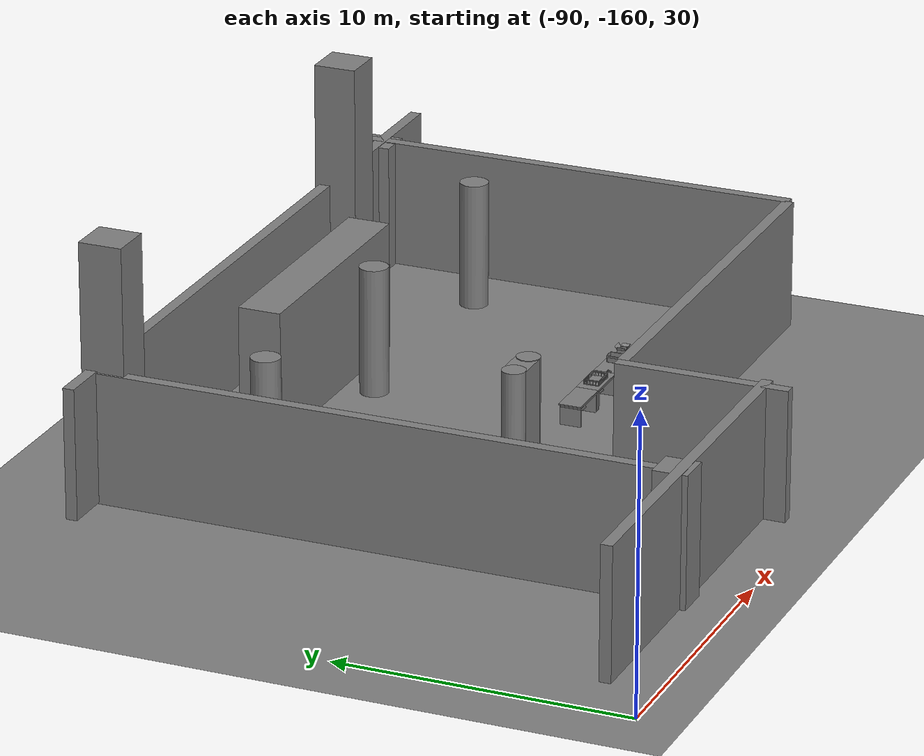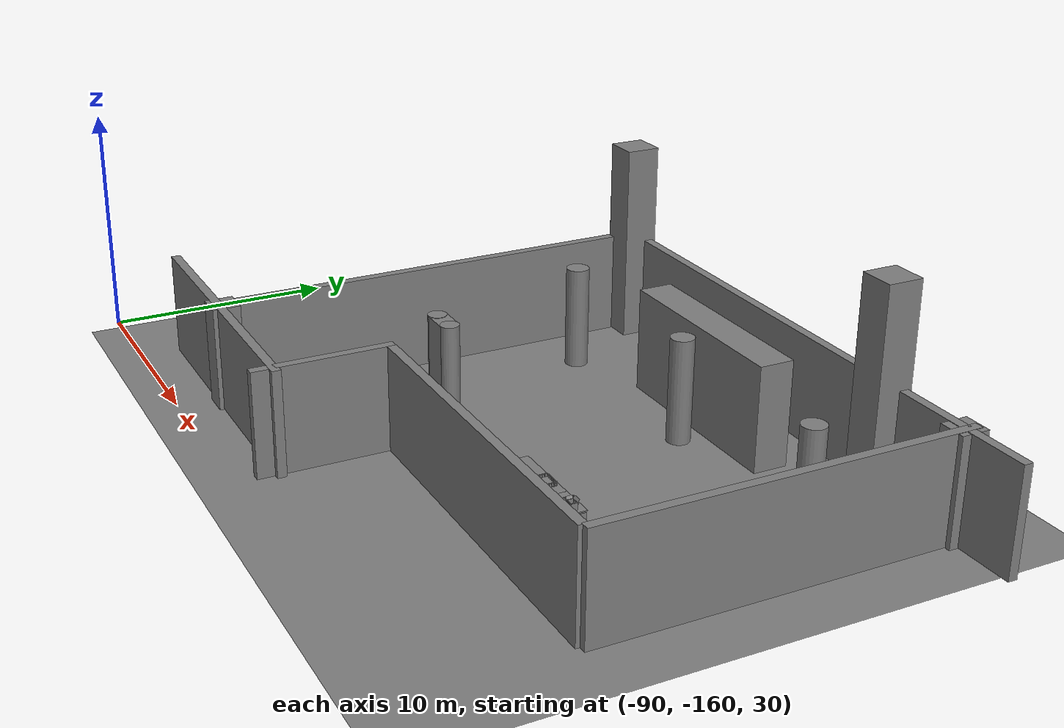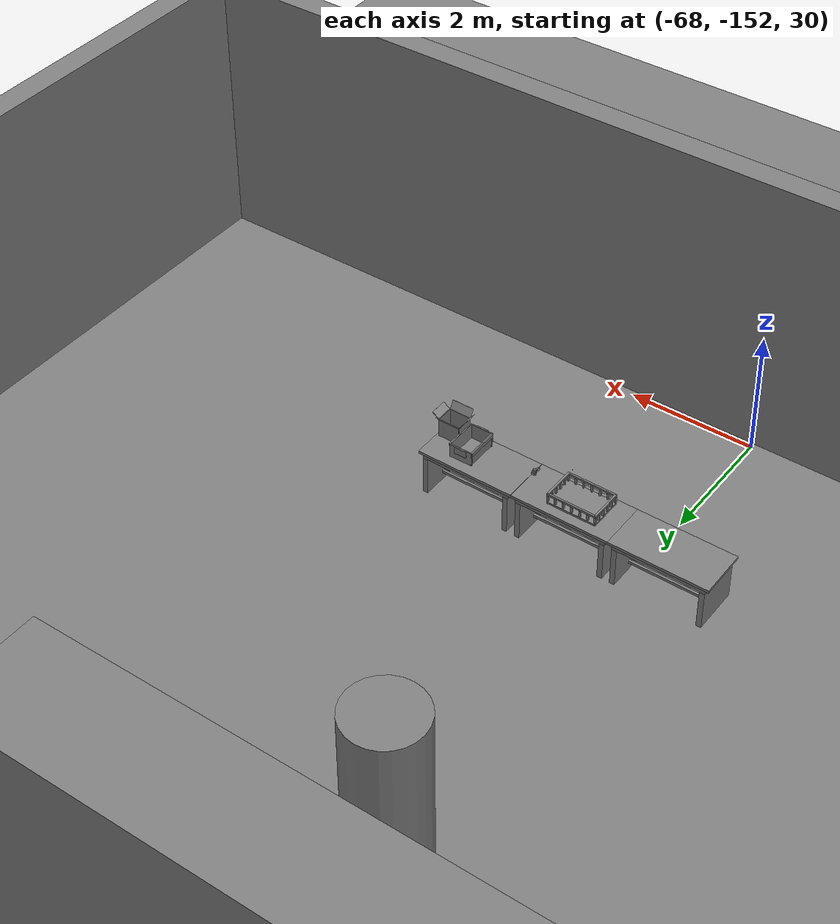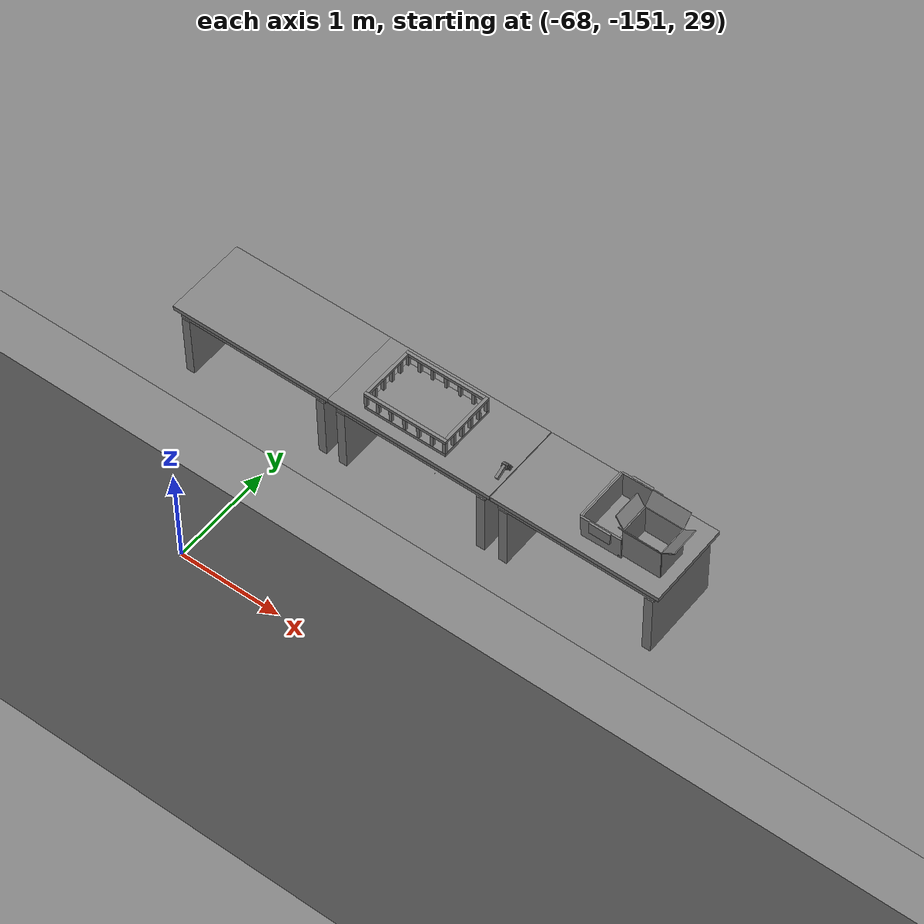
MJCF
<mujoco>
    <option gravity="0.000000000 0.000000000 -9.810000420" timestep="0.0049999999" integrator="implicitfast" density="1.225" viscosity="1.8000001e-05" noslip_iterations="10" iterations="100" sdf_iterations="50">
        <flag multiccd="disable"/>
    </option>
    <size memory="1000M"/>
    <compiler coordinate="local"/>
    <worldbody>
        <light cutoff="30" pos="0 1 1" dir="0 -1 -2"/>
        <light cutoff="30" pos="0 -1 1" dir="0 1 -2"/>
        <body pos="-64.866622925 -149.383972168 30.183746338" euler="89.999992371 89.999946594 0.000000000" name="openloong_gripper_2f85_fix_base_usda_bluebox_01">
            <geom contype="1" conaffinity="1" density="1000" type="box" material="" rgba="0.500000000 0.500000000 0.500000000 1.000000000" solimp="0.899999976 0.949999988 0.001000000" friction="1.000000000 0.005000000 0.000100000" solref="0.020000000 1.000000000" margin="0" condim="3" group="0" pos="0.276596069 0.187225342 0.000061035" quat="0.707107008 0.000077501 0.707106471 0.000077456" size="0.100000001 0.057999998 0.010000000" name="openloong_gripper_2f85_fix_base_usda_geom_9624EDCC_5ABB_44D8_A0D1_E6A2F8119DA2"/>
            <geom contype="1" conaffinity="1" density="1000" type="box" material="" rgba="0.500000000 0.500000000 0.500000000 1.000000000" solimp="0.899999976 0.949999988 0.001000000" friction="1.000000000 0.005000000 0.000100000" solref="0.020000000 1.000000000" margin="0" condim="3" group="0" pos="0.000000000 0.002883911 0.000000000" quat="1.000000000 0.000000000 0.000000000 0.000000000" size="0.254000008 0.003000000 0.172000006" name="openloong_gripper_2f85_fix_base_usda_geom_F31FE406_BA4F_44A4_8530_E97DEEC72DBE"/>
            <geom contype="1" conaffinity="1" density="1000" type="box" material="" rgba="0.500000000 0.500000000 0.500000000 1.000000000" solimp="0.899999976 0.949999988 0.001000000" friction="1.000000000 0.005000000 0.000100000" solref="0.020000000 1.000000000" margin="0" condim="3" group="0" pos="0.000015259 0.124874115 0.173477173" quat="0.999796450 0.020176515 -0.000000015 0.000000030" size="0.259999990 0.119999997 0.007000000" name="openloong_gripper_2f85_fix_base_usda_geom_91168497_E571_4AA7_81E7_AC4E5E8E9A7C"/>
            <geom contype="1" conaffinity="1" density="1000" type="box" material="" rgba="0.500000000 0.500000000 0.500000000 1.000000000" solimp="0.899999976 0.949999988 0.001000000" friction="1.000000000 0.005000000 0.000100000" solref="0.020000000 1.000000000" margin="0" condim="3" group="0" pos="0.000015259 0.124874115 -0.173477173" quat="0.999796450 -0.020176545 -0.000000015 0.000000000" size="0.259999990 0.119999997 0.007000000" name="openloong_gripper_2f85_fix_base_usda_geom_2D611650_A5D4_4936_82D7_630D756593D0"/>
            <geom contype="1" conaffinity="1" density="1000" type="box" material="" rgba="0.500000000 0.500000000 0.500000000 1.000000000" solimp="0.899999976 0.949999988 0.001000000" friction="1.000000000 0.005000000 0.000100000" solref="0.020000000 1.000000000" margin="0" condim="3" group="0" pos="0.000015259 0.214012146 0.188980103" quat="0.999913096 0.013176724 0.000000015 0.000000000" size="0.259999990 0.029999999 0.012500000" name="openloong_gripper_2f85_fix_base_usda_geom_456FA93C_BED0_4C69_9878_78EC96D6ECC5"/>
            <geom contype="1" conaffinity="1" density="1000" type="box" material="" rgba="0.500000000 0.500000000 0.500000000 1.000000000" solimp="0.899999976 0.949999988 0.001000000" friction="1.000000000 0.005000000 0.000100000" solref="0.020000000 1.000000000" margin="0" condim="3" group="0" pos="-0.258346558 0.125289917 0.001876831" quat="0.702796996 -0.020792052 0.710783184 0.020769238" size="0.189999998 0.119999997 0.009000000" name="openloong_gripper_2f85_fix_base_usda_geom_3C71E19E_2914_46E2_A3A9_4DDAF75C4E27"/>
            <geom contype="1" conaffinity="1" density="1000" type="box" material="" rgba="0.500000000 0.500000000 0.500000000 1.000000000" solimp="0.899999976 0.949999988 0.001000000" friction="1.000000000 0.005000000 0.000100000" solref="0.020000000 1.000000000" margin="0" condim="3" group="0" pos="0.000015259 0.214012146 -0.188980103" quat="0.999913096 -0.013176769 0.000000030 0.000000015" size="0.259999990 0.029999999 0.012500000" name="openloong_gripper_2f85_fix_base_usda_geom_5471D958_92A2_44E8_8CA7_7BED8F79EC51"/>
            <geom contype="1" conaffinity="1" density="1000" type="box" material="" rgba="0.500000000 0.500000000 0.500000000 1.000000000" solimp="0.899999976 0.949999988 0.001000000" friction="1.000000000 0.005000000 0.000100000" solref="0.020000000 1.000000000" margin="0" condim="3" group="0" pos="-0.276596069 0.187225342 0.000061035" quat="0.707106650 0.000077441 0.707106709 0.000077456" size="0.100000001 0.057999998 0.010000000" name="openloong_gripper_2f85_fix_base_usda_geom_95C57ADA_AF49_46D1_B557_51170ECCA511"/>
            <geom contype="1" conaffinity="1" density="1000" type="box" material="" rgba="0.500000000 0.500000000 0.500000000 1.000000000" solimp="0.899999976 0.949999988 0.001000000" friction="1.000000000 0.005000000 0.000100000" solref="0.020000000 1.000000000" margin="0" condim="3" group="0" pos="0.258346558 0.125289917 0.001876831" quat="0.702851534 0.018856451 0.710823834 -0.019329429" size="0.189999998 0.119999997 0.009000000" name="openloong_gripper_2f85_fix_base_usda_geom_B4A797E0_38FD_4EE3_94FD_C879B86605DA"/>
            <freejoint name="openloong_gripper_2f85_fix_base_usda_bluebox_01_joint"/>
            <site size="0.005000000 0.005000000 0.005000000" rgba="0.500000000 0.500000000 0.500000000 1.000000000" pos="0.000000000 0.000000000 0.000000000" quat="0.999961913 0.008726534 0.000000000 0.000000000" group="0" type="sphere" name="openloong_gripper_2f85_fix_base_usda_bluebox_01site"/>
        </body>
        <body pos="-64.496299744 -149.491867065 30.235729218" euler="0.000000000 0.000000000 89.999946594" name="openloong_gripper_2f85_fix_base_usda_cardboardbox_01">
            <geom contype="1" conaffinity="1" density="1000" type="box" material="" rgba="0.500000000 0.500000000 0.500000000 1.000000000" solimp="0.899999976 0.949999988 0.001000000" friction="1.000000000 0.005000000 0.000100000" solref="0.020000000 1.000000000" margin="0" condim="3" group="0" pos="-0.003166199 -0.004086494 0.005052090" quat="1.000000000 0.000000000 0.000000000 0.000000000" size="0.142499998 0.177500010 0.005000000" name="openloong_gripper_2f85_fix_base_usda_geom_DD1938ED_CE29_4B99_93E2_478360BFAA06"/>
            <geom contype="1" conaffinity="1" density="1000" type="box" material="" rgba="0.500000000 0.500000000 0.500000000 1.000000000" solimp="0.899999976 0.949999988 0.001000000" friction="1.000000000 0.005000000 0.000100000" solref="0.020000000 1.000000000" margin="0" condim="3" group="0" pos="-0.003166199 0.170316696 0.150570869" quat="1.000000000 0.000000000 0.000000000 0.000000000" size="0.142499998 0.005000000 0.149999991" name="openloong_gripper_2f85_fix_base_usda_geom_99F68597_9B1C_4F70_B0F7_9812155CFB7A"/>
            <geom contype="1" conaffinity="1" density="1000" type="box" material="" rgba="0.500000000 0.500000000 0.500000000 1.000000000" solimp="0.899999976 0.949999988 0.001000000" friction="1.000000000 0.005000000 0.000100000" solref="0.020000000 1.000000000" margin="0" condim="3" group="0" pos="-0.147399902 -0.005307198 0.150570869" quat="1.000000000 0.000000000 0.000000000 0.000000000" size="0.005000000 0.177500010 0.149999991" name="openloong_gripper_2f85_fix_base_usda_geom_11FEDFDF_63D3_45A3_A798_D60612BA53EC"/>
            <geom contype="1" conaffinity="1" density="1000" type="box" material="" rgba="0.500000000 0.500000000 0.500000000 1.000000000" solimp="0.899999976 0.949999988 0.001000000" friction="1.000000000 0.005000000 0.000100000" solref="0.020000000 1.000000000" margin="0" condim="3" group="0" pos="0.140275955 -0.005307198 0.150570869" quat="1.000000000 0.000000000 0.000000000 0.000000000" size="0.005000000 0.177500010 0.149999991" name="openloong_gripper_2f85_fix_base_usda_geom_8F33324E_F408_41C4_BA50_8EEB32DA6373"/>
            <geom contype="1" conaffinity="1" density="1000" type="box" material="" rgba="0.500000000 0.500000000 0.500000000 1.000000000" solimp="0.899999976 0.949999988 0.001000000" friction="1.000000000 0.005000000 0.000100000" solref="0.020000000 1.000000000" margin="0" condim="3" group="0" pos="-0.003166199 -0.181550980 0.150570869" quat="1.000000000 0.000000000 0.000000000 0.000000000" size="0.142499998 0.005000000 0.149999991" name="openloong_gripper_2f85_fix_base_usda_geom_FF1B2A14_8726_46E1_A2E5_FF2F9D9C5233"/>
            <freejoint name="openloong_gripper_2f85_fix_base_usda_cardboardbox_01_joint"/>
            <site size="0.005000000 0.005000000 0.005000000" rgba="0.500000000 0.500000000 0.500000000 1.000000000" pos="0.000000000 0.000000000 0.000000000" quat="0.999961913 0.008726535 0.000000000 0.000000000" group="0" type="sphere" name="openloong_gripper_2f85_fix_base_usda_site_A047B738_E9B5_4427_913F_1E17EF25D678"/>
            <body pos="0.139160156 -0.004048347 0.301930904" euler="-179.999954224 49.383502960 179.999954224" name="openloong_gripper_2f85_fix_base_usda_A1_006">
                <geom contype="1" conaffinity="1" density="1000" type="box" material="" rgba="0.500000000 0.500000000 0.500000000 1.000000000" solimp="0.899999976 0.949999988 0.001000000" friction="1.000000000 0.005000000 0.000100000" solref="0.020000000 1.000000000" margin="0" condim="3" group="0" pos="-0.071587563 0.000009537 0.001745224" quat="0.999999881 0.000000000 0.000000000 0.000000000" size="0.071249999 0.179999992 0.002500000" name="openloong_gripper_2f85_fix_base_usda_geom_31355FA6_5A6B_428D_BE7C_A374DA1312F2"/>
                <joint armature="0" stiffness="0.07" damping="0.0099999998" axis="0.000000 1.000000 0.000000" type="hinge" name="openloong_gripper_2f85_fix_base_usda_A1_006"/>
            </body>
            <body pos="-0.145902634 -0.004086494 0.301938057" euler="-180.000000000 -60.000011444 -180.000000000" name="openloong_gripper_2f85_fix_base_usda_A2_006">
                <geom contype="1" conaffinity="1" density="1000" type="box" material="" rgba="0.500000000 0.500000000 0.500000000 1.000000000" solimp="0.899999976 0.949999988 0.001000000" friction="1.000000000 0.005000000 0.000100000" solref="0.020000000 1.000000000" margin="0" condim="3" group="0" pos="0.071268082 0.000009537 0.002717972" quat="0.000002921 0.000000000 -0.000000030 0.999999881" size="0.071249999 0.179999992 0.002500000" name="openloong_gripper_2f85_fix_base_usda_geom_6BF3DF7D_795D_4799_ADC8_D70D29D653C3"/>
                <joint armature="0" stiffness="0.07" damping="0.0099999998" axis="0.000000 1.000000 0.000000" type="hinge" name="openloong_gripper_2f85_fix_base_usda_A2_006"/>
            </body>
            <body pos="-0.003385544 0.175991058 0.301930904" euler="-125.858116150 -0.000004561 0.000002331" name="openloong_gripper_2f85_fix_base_usda_B2_006">
                <geom contype="1" conaffinity="1" density="1000" type="box" material="" rgba="0.500000000 0.500000000 0.500000000 1.000000000" solimp="0.899999976 0.949999988 0.001000000" friction="1.000000000 0.005000000 0.000100000" solref="0.020000000 1.000000000" margin="0" condim="3" group="0" pos="0.000009537 -0.070939064 -0.002470016" quat="0.999614120 0.027776197 -0.000000015 0.000000030" size="0.137500003 0.064999998 0.005000000" name="openloong_gripper_2f85_fix_base_usda_geom_0FADB10E_4E57_4BC0_AFF5_D95FC044AEC7"/>
                <joint armature="0" stiffness="0.07" damping="0.0099999998" axis="1.000000 0.000000 0.000000" type="hinge" name="openloong_gripper_2f85_fix_base_usda_B2_006"/>
            </body>
            <body pos="-0.003385544 -0.184140205 0.301938057" euler="147.805557251 0.000000000 0.000000000" name="openloong_gripper_2f85_fix_base_usda_B1_006">
                <geom contype="1" conaffinity="1" density="1000" type="box" material="" rgba="0.500000000 0.500000000 0.500000000 1.000000000" solimp="0.899999976 0.949999988 0.001000000" friction="1.000000000 0.005000000 0.000100000" solref="0.020000000 1.000000000" margin="0" condim="3" group="0" pos="-0.000028610 0.070202351 -0.002703667" quat="0.999614179 -0.027776167 0.000000000 0.000000000" size="0.137500003 0.064999998 0.005000000" name="openloong_gripper_2f85_fix_base_usda_geom_40E0719C_B510_457D_9406_754DEB4063B5"/>
                <joint armature="0" stiffness="0.07" damping="0.0099999998" axis="1.000000 0.000000 0.000000" type="hinge" name="openloong_gripper_2f85_fix_base_usda_B1_006"/>
            </body>
        </body>
        <body pos="-65.882858276 -149.481979370 30.229999542" euler="-64.487716675 0.000000000 0.000000000" name="openloong_gripper_2f85_fix_base_usda_Barcode">
            <geom contype="1" conaffinity="1" density="1000" type="box" material="" rgba="0.500000000 0.500000000 0.500000000 1.000000000" solimp="0.899999976 0.949999988 0.001000000" friction="1.000000000 0.005000000 0.000100000" solref="0.020000000 1.000000000" margin="0" condim="3" group="0" pos="0.000000000 0.013038635 0.001419067" quat="0.000000000 0.000000000 0.000000000 1.000000119" size="0.034000002 0.010000000 0.017999999" name="openloong_gripper_2f85_fix_base_usda_geom_A81308ED_2287_4C8C_AE47_414FD24B512C"/>
            <geom contype="1" conaffinity="1" density="1000" type="box" material="" rgba="0.500000000 0.500000000 0.500000000 1.000000000" solimp="0.899999976 0.949999988 0.001000000" friction="1.000000000 0.005000000 0.000100000" solref="0.020000000 1.000000000" margin="0" condim="3" group="0" pos="0.000000000 -0.035301208 -0.007095337" quat="0.000000000 0.000000000 -0.043619365 0.999048233" size="0.028999999 0.010000000 0.020000000" name="openloong_gripper_2f85_fix_base_usda_geom_A743C70B_BBDF_4968_B79B_BAD0DE308F46"/>
            <geom contype="1" conaffinity="1" density="1000" type="box" material="" rgba="0.500000000 0.500000000 0.500000000 1.000000000" solimp="0.899999976 0.949999988 0.001000000" friction="1.000000000 0.005000000 0.000100000" solref="0.020000000 1.000000000" margin="0" condim="3" group="0" pos="0.000000000 -0.043411255 -0.011749268" quat="0.922262907 0.386563420 0.000000000 0.000000000" size="0.026000001 0.010000000 0.020000000" name="openloong_gripper_2f85_fix_base_usda_geom_6E086D5B_2C2D_4FBC_98F1_DD8B6243AC1F"/>
            <geom contype="1" conaffinity="1" density="1000" type="box" material="" rgba="0.500000000 0.500000000 0.500000000 1.000000000" solimp="0.899999976 0.949999988 0.001000000" friction="1.000000000 0.005000000 0.000100000" solref="0.020000000 1.000000000" margin="0" condim="3" group="0" pos="0.000000000 -0.016967773 -0.031860352" quat="0.000000000 0.000000000 0.000000000 1.000000119" size="0.008000000 0.010000000 0.013000000" name="openloong_gripper_2f85_fix_base_usda_geom_CA08DEA9_037B_4812_BAE5_801482243201"/>
            <geom contype="1" conaffinity="1" density="1000" type="box" material="" rgba="0.500000000 0.500000000 0.500000000 1.000000000" solimp="0.899999976 0.949999988 0.001000000" friction="1.000000000 0.005000000 0.000100000" solref="0.020000000 1.000000000" margin="0" condim="3" group="0" pos="0.000000000 -0.001869202 0.000312805" quat="0.953716993 0.300705761 0.000000000 0.000000000" size="0.032000002 0.010000000 0.018999999" name="openloong_gripper_2f85_fix_base_usda_geom_BCD98648_FDAE_43C3_A144_D5EB97FAF40B"/>
            <geom contype="1" conaffinity="1" density="1000" type="box" material="" rgba="0.500000000 0.500000000 0.500000000 1.000000000" solimp="0.899999976 0.949999988 0.001000000" friction="1.000000000 0.005000000 0.000100000" solref="0.020000000 1.000000000" margin="0" condim="3" group="0" pos="0.000000000 -0.019531250 -0.003173828" quat="0.953716993 0.300705761 0.000000000 0.000000000" size="0.030999999 0.010000000 0.020000000" name="openloong_gripper_2f85_fix_base_usda_geom_39C7A308_FAAC_455E_AF7F_2F680EF186C1"/>
            <geom contype="1" conaffinity="1" density="1000" type="box" material="" rgba="0.500000000 0.500000000 0.500000000 1.000000000" solimp="0.899999976 0.949999988 0.001000000" friction="1.000000000 0.005000000 0.000100000" solref="0.020000000 1.000000000" margin="0" condim="3" group="0" pos="0.000000000 -0.035301208 -0.007095337" quat="0.953716993 0.300705761 0.000000000 0.000000000" size="0.028999999 0.010000000 0.020000000" name="openloong_gripper_2f85_fix_base_usda_geom_F66900E2_3AB6_4F65_BAF2_EC7C7B49C147"/>
            <geom contype="1" conaffinity="1" density="1000" type="box" material="" rgba="0.500000000 0.500000000 0.500000000 1.000000000" solimp="0.899999976 0.949999988 0.001000000" friction="1.000000000 0.005000000 0.000100000" solref="0.020000000 1.000000000" margin="0" condim="3" group="0" pos="0.000000000 -0.042617798 -0.071121216" quat="0.000000000 0.000000000 0.000000000 1.000000119" size="0.013000000 0.021000000 0.059999999" name="openloong_gripper_2f85_fix_base_usda_geom_55DE5511_7F4C_4B0C_9EEA_9696CC3B0A20"/>
            <freejoint name="openloong_gripper_2f85_fix_base_usda_Barcode_joint"/>
            <site size="0.005000000 0.005000000 0.005000000" rgba="0.500000000 0.500000000 0.500000000 1.000000000" pos="0.000000000 0.000000000 0.000000000" quat="1.000000000 0.000000000 0.000000000 0.000000000" group="0" type="sphere" name="openloong_gripper_2f85_fix_base_usda_Barcode_site"/>
        </body>
        <body pos="-66.745018005 -149.392349243 30.184000015" euler="0.000000000 0.000000000 89.999946594" name="[22332667781232]_Basket_01">
            <geom contype="1" conaffinity="1" density="1000" type="box" material="" rgba="0.500000000 0.500000000 0.500000000 1.000000000" solimp="0.899999976 0.949999988 0.001000000" friction="1.000000000 0.005000000 0.000100000" solref="0.020000000 1.000000000" margin="0" condim="3" group="0" pos="-0.052425385 0.389207840 0.089787483" quat="0.707107008 0.000000000 0.000000000 0.707106411" size="0.014249999 0.014249999 0.059999999" name="[22332667781232]_geom_AC56E211_A0BA_47DB_A72E_B0153D1FC845"/>
            <geom contype="1" conaffinity="1" density="1000" type="box" material="" rgba="0.500000000 0.500000000 0.500000000 1.000000000" solimp="0.899999976 0.949999988 0.001000000" friction="1.000000000 0.005000000 0.000100000" solref="0.020000000 1.000000000" margin="0" condim="3" group="0" pos="0.264015198 -0.133043289 0.089787483" quat="0.707107008 0.000000000 0.000000000 0.707106411" size="0.014249999 0.014249999 0.059999999" name="[22332667781232]_geom_AD61B435_8F16_42E3_A732_0A41FEB9FBAD"/>
            <geom contype="1" conaffinity="1" density="1000" type="box" material="" rgba="0.500000000 0.500000000 0.500000000 1.000000000" solimp="0.899999976 0.949999988 0.001000000" friction="1.000000000 0.005000000 0.000100000" solref="0.020000000 1.000000000" margin="0" condim="3" group="0" pos="-0.264015198 -0.265548706 0.089793205" quat="0.707107008 0.000000000 0.000000000 0.707106411" size="0.014249999 0.014249999 0.059999999" name="[22332667781232]_geom_A46D3931_E429_47E8_9C4C_59755CA4A17A"/>
            <geom contype="1" conaffinity="1" density="1000" type="box" material="" rgba="0.500000000 0.500000000 0.500000000 1.000000000" solimp="0.899999976 0.949999988 0.001000000" friction="1.000000000 0.005000000 0.000100000" solref="0.020000000 1.000000000" margin="0" condim="3" group="0" pos="-0.160263062 -0.389322281 0.089793205" quat="0.707107008 0.000000000 0.000000000 0.707106411" size="0.014249999 0.014249999 0.059999999" name="[22332667781232]_geom_5C1D34CA_29C1_4D8B_BD4D_2C583A71B4DA"/>
            <geom contype="1" conaffinity="1" density="1000" type="box" material="" rgba="0.500000000 0.500000000 0.500000000 1.000000000" solimp="0.899999976 0.949999988 0.001000000" friction="1.000000000 0.005000000 0.000100000" solref="0.020000000 1.000000000" margin="0" condim="3" group="0" pos="0.162265778 -0.389322281 0.089787483" quat="0.707107008 0.000000000 0.000000000 0.707106411" size="0.014249999 0.014249999 0.059999999" name="[22332667781232]_geom_0D6ADCE7_C76D_45F5_B143_172148F85093"/>
            <geom contype="1" conaffinity="1" density="1000" type="box" material="" rgba="0.500000000 0.500000000 0.500000000 1.000000000" solimp="0.899999976 0.949999988 0.001000000" friction="1.000000000 0.005000000 0.000100000" solref="0.020000000 1.000000000" margin="0" condim="3" group="0" pos="0.264015198 0.389207840 0.089787483" quat="0.707107008 0.000000000 0.000000000 0.707106411" size="0.014249999 0.014249999 0.059999999" name="[22332667781232]_geom_0C2D372C_3F21_4E9A_9B54_524BC2B3246A"/>
            <geom contype="1" conaffinity="1" density="1000" type="box" material="" rgba="0.500000000 0.500000000 0.500000000 1.000000000" solimp="0.899999976 0.949999988 0.001000000" friction="1.000000000 0.005000000 0.000100000" solref="0.020000000 1.000000000" margin="0" condim="3" group="0" pos="-0.264015198 -0.133043289 0.089793205" quat="0.707107008 0.000000000 0.000000000 0.707106411" size="0.014249999 0.014249999 0.059999999" name="[22332667781232]_geom_8CEFAF52_3261_4D1D_AA27_CD2DE321E2C8"/>
            <geom contype="1" conaffinity="1" density="1000" type="box" material="" rgba="0.500000000 0.500000000 0.500000000 1.000000000" solimp="0.899999976 0.949999988 0.001000000" friction="1.000000000 0.005000000 0.000100000" solref="0.020000000 1.000000000" margin="0" condim="3" group="0" pos="-0.264026642 0.269256592 0.089793205" quat="0.707107008 0.000000000 0.000000000 0.707106411" size="0.014249999 0.014249999 0.059999999" name="[22332667781232]_geom_61649324_6593_47EF_BE04_879B8770F63E"/>
            <geom contype="1" conaffinity="1" density="1000" type="box" material="" rgba="0.500000000 0.500000000 0.500000000 1.000000000" solimp="0.899999976 0.949999988 0.001000000" friction="1.000000000 0.005000000 0.000100000" solref="0.020000000 1.000000000" margin="0" condim="3" group="0" pos="0.054462433 0.389207840 0.089787483" quat="0.707107008 0.000000000 0.000000000 0.707106411" size="0.014249999 0.014249999 0.059999999" name="[22332667781232]_geom_927F7B3F_6E41_46B7_B395_915F0E04D8EA"/>
            <geom contype="1" conaffinity="1" density="1000" type="box" material="" rgba="0.500000000 0.500000000 0.500000000 1.000000000" solimp="0.899999976 0.949999988 0.001000000" friction="1.000000000 0.005000000 0.000100000" solref="0.020000000 1.000000000" margin="0" condim="3" group="0" pos="0.054462433 -0.389322281 0.089787483" quat="0.707107008 0.000000000 0.000000000 0.707106411" size="0.014249999 0.014249999 0.059999999" name="[22332667781232]_geom_C10FC0E1_9A37_43AE_935D_1BF22F3EA85A"/>
            <geom contype="1" conaffinity="1" density="1000" type="box" material="" rgba="0.500000000 0.500000000 0.500000000 1.000000000" solimp="0.899999976 0.949999988 0.001000000" friction="1.000000000 0.005000000 0.000100000" solref="0.020000000 1.000000000" margin="0" condim="3" group="0" pos="0.264015198 0.269256592 0.089793205" quat="0.707107008 0.000000000 0.000000000 0.707106411" size="0.014249999 0.014249999 0.059999999" name="[22332667781232]_geom_58A5BFF2_572A_489B_80E4_EC6EB82030E7"/>
            <geom contype="1" conaffinity="1" density="1000" type="box" material="" rgba="0.500000000 0.500000000 0.500000000 1.000000000" solimp="0.899999976 0.949999988 0.001000000" friction="1.000000000 0.005000000 0.000100000" solref="0.020000000 1.000000000" margin="0" condim="3" group="0" pos="0.264015198 -0.389322281 0.089787483" quat="0.707107008 0.000000000 0.000000000 0.707106411" size="0.014249999 0.014249999 0.059999999" name="[22332667781232]_geom_0DF388D1_D8C3_420B_8C94_8308A7EF2EC4"/>
            <geom contype="1" conaffinity="1" density="1000" type="box" material="" rgba="0.500000000 0.500000000 0.500000000 1.000000000" solimp="0.899999976 0.949999988 0.001000000" friction="1.000000000 0.005000000 0.000100000" solref="0.020000000 1.000000000" margin="0" condim="3" group="0" pos="0.000000000 0.000000000 0.015998840" quat="0.707107008 0.000000000 0.000000000 0.707106411" size="0.403499991 0.279000014 0.015750000" name="[22332667781232]_geom_C0B65730_E96B_4646_B200_95B53277F92E"/>
            <geom contype="1" conaffinity="1" density="1000" type="box" material="" rgba="0.500000000 0.500000000 0.500000000 1.000000000" solimp="0.899999976 0.949999988 0.001000000" friction="1.000000000 0.005000000 0.000100000" solref="0.020000000 1.000000000" margin="0" condim="3" group="0" pos="0.000000000 -0.389476776 0.163619041" quat="0.707107008 0.000000000 0.000000000 0.707106411" size="0.015000000 0.277500004 0.015750000" name="[22332667781232]_geom_035578FA_9B47_4BB5_89CD_8BF2995D5ABE"/>
            <geom contype="1" conaffinity="1" density="1000" type="box" material="" rgba="0.500000000 0.500000000 0.500000000 1.000000000" solimp="0.899999976 0.949999988 0.001000000" friction="1.000000000 0.005000000 0.000100000" solref="0.020000000 1.000000000" margin="0" condim="3" group="0" pos="0.162265778 0.389207840 0.089787483" quat="0.707107008 0.000000000 0.000000000 0.707106411" size="0.014249999 0.014249999 0.059999999" name="[22332667781232]_geom_FA735942_5DCC_4C26_8095_3DAA35C20209"/>
            <geom contype="1" conaffinity="1" density="1000" type="box" material="" rgba="0.500000000 0.500000000 0.500000000 1.000000000" solimp="0.899999976 0.949999988 0.001000000" friction="1.000000000 0.005000000 0.000100000" solref="0.020000000 1.000000000" margin="0" condim="3" group="0" pos="0.000000000 0.389471054 0.163619041" quat="0.707107008 0.000000000 0.000000000 0.707106411" size="0.015000000 0.277500004 0.015750000" name="[22332667781232]_geom_B75A216A_E771_4AE1_B50F_B0C9D9A04421"/>
            <geom contype="1" conaffinity="1" density="1000" type="box" material="" rgba="0.500000000 0.500000000 0.500000000 1.000000000" solimp="0.899999976 0.949999988 0.001000000" friction="1.000000000 0.005000000 0.000100000" solref="0.020000000 1.000000000" margin="0" condim="3" group="0" pos="-0.263511658 0.000000000 0.163619041" quat="0.707107008 0.000000000 0.000000000 0.707106411" size="0.403499991 0.015000000 0.015750000" name="[22332667781232]_geom_1D75EDCA_A7A5_4AEF_902D_D2C64297FEF9"/>
            <geom contype="1" conaffinity="1" density="1000" type="box" material="" rgba="0.500000000 0.500000000 0.500000000 1.000000000" solimp="0.899999976 0.949999988 0.001000000" friction="1.000000000 0.005000000 0.000100000" solref="0.020000000 1.000000000" margin="0" condim="3" group="0" pos="-0.264015198 0.141334534 0.089793205" quat="0.707107008 0.000000000 0.000000000 0.707106411" size="0.014249999 0.014249999 0.059999999" name="[22332667781232]_geom_C5037F59_D1D4_49CD_A685_6EAEE3BBA775"/>
            <geom contype="1" conaffinity="1" density="1000" type="box" material="" rgba="0.500000000 0.500000000 0.500000000 1.000000000" solimp="0.899999976 0.949999988 0.001000000" friction="1.000000000 0.005000000 0.000100000" solref="0.020000000 1.000000000" margin="0" condim="3" group="0" pos="0.264015198 -0.265548706 0.089787483" quat="0.707107008 0.000000000 0.000000000 0.707106411" size="0.014249999 0.014249999 0.059999999" name="[22332667781232]_geom_24A0E67E_42D4_4878_8A27_6659C4928D5E"/>
            <geom contype="1" conaffinity="1" density="1000" type="box" material="" rgba="0.500000000 0.500000000 0.500000000 1.000000000" solimp="0.899999976 0.949999988 0.001000000" friction="1.000000000 0.005000000 0.000100000" solref="0.020000000 1.000000000" margin="0" condim="3" group="0" pos="-0.160263062 0.389207840 0.089787483" quat="0.707107008 0.000000000 0.000000000 0.707106411" size="0.014249999 0.014249999 0.059999999" name="[22332667781232]_geom_7B37B876_78B6_4797_8B84_942AA26C4B9F"/>
            <geom contype="1" conaffinity="1" density="1000" type="box" material="" rgba="0.500000000 0.500000000 0.500000000 1.000000000" solimp="0.899999976 0.949999988 0.001000000" friction="1.000000000 0.005000000 0.000100000" solref="0.020000000 1.000000000" margin="0" condim="3" group="0" pos="-0.052425385 -0.389322281 0.089787483" quat="0.707107008 0.000000000 0.000000000 0.707106411" size="0.014249999 0.014249999 0.059999999" name="[22332667781232]_geom_79033D6E_33A2_4C0F_A498_1753AAB4FC91"/>
            <geom contype="1" conaffinity="1" density="1000" type="box" material="" rgba="0.500000000 0.500000000 0.500000000 1.000000000" solimp="0.899999976 0.949999988 0.001000000" friction="1.000000000 0.005000000 0.000100000" solref="0.020000000 1.000000000" margin="0" condim="3" group="0" pos="-0.264026642 -0.389322281 0.089793205" quat="0.707107008 0.000000000 0.000000000 0.707106411" size="0.014249999 0.014249999 0.059999999" name="[22332667781232]_geom_3955DAB0_8971_4642_98E6_97E0FF9C13AC"/>
            <geom contype="1" conaffinity="1" density="1000" type="box" material="" rgba="0.500000000 0.500000000 0.500000000 1.000000000" solimp="0.899999976 0.949999988 0.001000000" friction="1.000000000 0.005000000 0.000100000" solref="0.020000000 1.000000000" margin="0" condim="3" group="0" pos="0.264015198 0.141334534 0.089787483" quat="0.707107008 0.000000000 0.000000000 0.707106411" size="0.014249999 0.014249999 0.059999999" name="[22332667781232]_geom_21796691_2A36_49EC_B4D9_EAD85CD99F11"/>
            <geom contype="1" conaffinity="1" density="1000" type="box" material="" rgba="0.500000000 0.500000000 0.500000000 1.000000000" solimp="0.899999976 0.949999988 0.001000000" friction="1.000000000 0.005000000 0.000100000" solref="0.020000000 1.000000000" margin="0" condim="3" group="0" pos="-0.264015198 0.389207840 0.089793205" quat="0.707107008 0.000000000 0.000000000 0.707106411" size="0.014249999 0.014249999 0.059999999" name="[22332667781232]_geom_266E4CB2_7825_446E_B8C3_2CC12F29BF82"/>
            <geom contype="1" conaffinity="1" density="1000" type="box" material="" rgba="0.500000000 0.500000000 0.500000000 1.000000000" solimp="0.899999976 0.949999988 0.001000000" friction="1.000000000 0.005000000 0.000100000" solref="0.020000000 1.000000000" margin="0" condim="3" group="0" pos="0.264015198 0.004480362 0.089787483" quat="0.707107008 0.000000000 0.000000000 0.707106411" size="0.014249999 0.014249999 0.059999999" name="[22332667781232]_geom_D516A32F_8160_4852_8E61_27B5F44969AE"/>
            <geom contype="1" conaffinity="1" density="1000" type="box" material="" rgba="0.500000000 0.500000000 0.500000000 1.000000000" solimp="0.899999976 0.949999988 0.001000000" friction="1.000000000 0.005000000 0.000100000" solref="0.020000000 1.000000000" margin="0" condim="3" group="0" pos="0.263694763 -0.000011444 0.163619041" quat="0.707107008 0.000000000 0.000000000 0.707106411" size="0.403499991 0.015000000 0.015750000" name="[22332667781232]_geom_DB34EC2D_40DE_4162_B5B4_CF7F4F374C49"/>
            <geom contype="1" conaffinity="1" density="1000" type="box" material="" rgba="0.500000000 0.500000000 0.500000000 1.000000000" solimp="0.899999976 0.949999988 0.001000000" friction="1.000000000 0.005000000 0.000100000" solref="0.020000000 1.000000000" margin="0" condim="3" group="0" pos="-0.264015198 0.004480362 0.089793205" quat="0.707107008 0.000000000 0.000000000 0.707106411" size="0.014249999 0.014249999 0.059999999" name="[22332667781232]_geom_06504755_D1A2_43AA_8ECA_0F823F1E8CB0"/>
            <freejoint name="[22332667781232]_joint_CA3D5F9A_1DB2_4132_AB55_94C31A74375C"/>
        </body>
        <body pos="0.000000000 0.000000000 0.000000000" euler="0.000000000 0.000000000 0.000000000" name="Static Objects_Static Objects">
            <geom contype="1" conaffinity="1" density="1000" type="box" material="" rgba="0.500000000 0.500000000 0.500000000 1.000000000" solimp="0.899999976 0.949999988 0.001000000" friction="1.000000000 0.005000000 0.000100000" solref="0.020000000 1.000000000" margin="0" condim="3" group="0" pos="-67.544113159 -149.365814209 29.727830887" quat="0.500000417 0.499999970 0.499999553 0.499999970" size="0.381000012 0.319999993 0.041000001" name="Static Objects_geom_EB4ACC37_00A6_433F_BEAC_BB6155383D64"/>
            <geom contype="1" conaffinity="1" density="1000" type="box" material="" rgba="0.500000000 0.500000000 0.500000000 1.000000000" solimp="0.899999976 0.949999988 0.001000000" friction="1.000000000 0.005000000 0.000100000" solref="0.020000000 1.000000000" margin="0" condim="3" group="0" pos="-68.239501953 -149.365814209 30.086868286" quat="0.500000417 0.499999970 0.499999553 0.499999970" size="0.370999992 0.039500002 0.745000005" name="Static Objects_geom_ACC47534_6608_4411_9DB3_5290392D9173"/>
            <geom contype="1" conaffinity="1" density="1000" type="box" material="" rgba="0.500000000 0.500000000 0.500000000 1.000000000" solimp="0.899999976 0.949999988 0.001000000" friction="1.000000000 0.005000000 0.000100000" solref="0.020000000 1.000000000" margin="0" condim="3" group="0" pos="-68.239501953 -149.365814209 30.147235870" quat="0.500000417 0.499999970 0.499999553 0.499999970" size="0.400000006 0.022000000 0.800000012" name="Static Objects_geom_850CF4B8_2480_4A5E_99D7_C637D588D647"/>
            <geom contype="1" conaffinity="1" density="1000" type="box" material="" rgba="0.500000000 0.500000000 0.500000000 1.000000000" solimp="0.899999976 0.949999988 0.001000000" friction="1.000000000 0.005000000 0.000100000" solref="0.020000000 1.000000000" margin="0" condim="3" group="0" pos="-68.934890747 -149.365814209 29.727830887" quat="0.500000417 0.499999970 0.499999553 0.499999970" size="0.381000012 0.319999993 0.041000001" name="Static Objects_geom_A641A1F9_0CE7_4DEC_B6F2_51D9DF630E53"/>
            <geom contype="1" conaffinity="1" density="1000" type="box" material="" rgba="0.500000000 0.500000000 0.500000000 1.000000000" solimp="0.899999976 0.949999988 0.001000000" friction="1.000000000 0.005000000 0.000100000" solref="0.020000000 1.000000000" margin="0" condim="3" group="0" pos="-68.239501953 -149.365814209 29.561563492" quat="0.500000417 0.499999970 0.499999553 0.499999970" size="0.020000000 0.022000000 0.660000026" name="Static Objects_geom_E047987A_2411_4DA3_9C7B_0C29F8518A5E"/>
            <geom contype="1" conaffinity="1" density="1000" type="box" material="" rgba="0.500000000 0.500000000 0.500000000 1.000000000" solimp="0.899999976 0.949999988 0.001000000" friction="1.000000000 0.005000000 0.000100000" solref="0.020000000 1.000000000" margin="0" condim="3" group="0" pos="-65.945671082 -149.365814209 29.727830887" quat="0.500000417 0.499999970 0.499999553 0.499999970" size="0.381000012 0.319999993 0.041000001" name="Static Objects_geom_AB1218D9_764F_42D0_921E_4EAF29C9DEBF"/>
            <geom contype="1" conaffinity="1" density="1000" type="box" material="" rgba="0.500000000 0.500000000 0.500000000 1.000000000" solimp="0.899999976 0.949999988 0.001000000" friction="1.000000000 0.005000000 0.000100000" solref="0.020000000 1.000000000" margin="0" condim="3" group="0" pos="-66.641059875 -149.365814209 30.086868286" quat="0.500000417 0.499999970 0.499999553 0.499999970" size="0.370999992 0.039500002 0.745000005" name="Static Objects_geom_E123863C_241F_4017_8D07_53E96A4C21B9"/>
            <geom contype="1" conaffinity="1" density="1000" type="box" material="" rgba="0.500000000 0.500000000 0.500000000 1.000000000" solimp="0.899999976 0.949999988 0.001000000" friction="1.000000000 0.005000000 0.000100000" solref="0.020000000 1.000000000" margin="0" condim="3" group="0" pos="-66.641059875 -149.365814209 30.147235870" quat="0.500000417 0.499999970 0.499999553 0.499999970" size="0.400000006 0.022000000 0.800000012" name="Static Objects_geom_037FE58E_87EA_47AB_A180_6AC1C58A7982"/>
            <geom contype="1" conaffinity="1" density="1000" type="box" material="" rgba="0.500000000 0.500000000 0.500000000 1.000000000" solimp="0.899999976 0.949999988 0.001000000" friction="1.000000000 0.005000000 0.000100000" solref="0.020000000 1.000000000" margin="0" condim="3" group="0" pos="-67.336448669 -149.365814209 29.727830887" quat="0.500000417 0.499999970 0.499999553 0.499999970" size="0.381000012 0.319999993 0.041000001" name="Static Objects_geom_22AE8BB5_6990_4A6C_9A1F_CFCE1091AC22"/>
            <geom contype="1" conaffinity="1" density="1000" type="box" material="" rgba="0.500000000 0.500000000 0.500000000 1.000000000" solimp="0.899999976 0.949999988 0.001000000" friction="1.000000000 0.005000000 0.000100000" solref="0.020000000 1.000000000" margin="0" condim="3" group="0" pos="-66.641059875 -149.365814209 29.561563492" quat="0.500000417 0.499999970 0.499999553 0.499999970" size="0.020000000 0.022000000 0.660000026" name="Static Objects_geom_49B4490E_9782_42A8_AFE9_C78BB01C7F79"/>
            <geom contype="1" conaffinity="1" density="1000" type="box" material="" rgba="0.500000000 0.500000000 0.500000000 1.000000000" solimp="0.899999976 0.949999988 0.001000000" friction="1.000000000 0.005000000 0.000100000" solref="0.020000000 1.000000000" margin="0" condim="3" group="0" pos="-64.338577271 -149.365814209 29.727830887" quat="0.500000417 0.499999970 0.499999553 0.499999970" size="0.381000012 0.319999993 0.041000001" name="Static Objects_geom_DF07F4A5_41E6_4764_B952_3730267FE108"/>
            <geom contype="1" conaffinity="1" density="1000" type="box" material="" rgba="0.500000000 0.500000000 0.500000000 1.000000000" solimp="0.899999976 0.949999988 0.001000000" friction="1.000000000 0.005000000 0.000100000" solref="0.020000000 1.000000000" margin="0" condim="3" group="0" pos="-65.033966064 -149.365814209 30.086868286" quat="0.500000417 0.499999970 0.499999553 0.499999970" size="0.370999992 0.039500002 0.745000005" name="Static Objects_geom_9934F153_F11A_4948_B7DE_F059B962E54E"/>
            <geom contype="1" conaffinity="1" density="1000" type="box" material="" rgba="0.500000000 0.500000000 0.500000000 1.000000000" solimp="0.899999976 0.949999988 0.001000000" friction="1.000000000 0.005000000 0.000100000" solref="0.020000000 1.000000000" margin="0" condim="3" group="0" pos="-65.033966064 -149.365814209 30.147235870" quat="0.500000417 0.499999970 0.499999553 0.499999970" size="0.400000006 0.022000000 0.800000012" name="Static Objects_geom_C9C72A53_8177_4308_9264_A01018718910"/>
            <geom contype="1" conaffinity="1" density="1000" type="box" material="" rgba="0.500000000 0.500000000 0.500000000 1.000000000" solimp="0.899999976 0.949999988 0.001000000" friction="1.000000000 0.005000000 0.000100000" solref="0.020000000 1.000000000" margin="0" condim="3" group="0" pos="-65.729354858 -149.365814209 29.727830887" quat="0.500000417 0.499999970 0.499999553 0.499999970" size="0.381000012 0.319999993 0.041000001" name="Static Objects_geom_514B13C7_3BBF_4203_BB05_32040DA7FB1E"/>
            <geom contype="1" conaffinity="1" density="1000" type="box" material="" rgba="0.500000000 0.500000000 0.500000000 1.000000000" solimp="0.899999976 0.949999988 0.001000000" friction="1.000000000 0.005000000 0.000100000" solref="0.020000000 1.000000000" margin="0" condim="3" group="0" pos="-65.033966064 -149.365814209 29.561563492" quat="0.500000417 0.499999970 0.499999553 0.499999970" size="0.020000000 0.022000000 0.660000026" name="Static Objects_geom_7E7A1669_6C40_4A11_818E_5C44DC334CFC"/>
            <geom contype="1" conaffinity="1" density="1000" type="box" material="" rgba="0.500000000 0.500000000 0.500000000 1.000000000" solimp="0.899999976 0.949999988 0.001000000" friction="1.000000000 0.005000000 0.000100000" solref="0.020000000 1.000000000" margin="0" condim="3" group="0" pos="-61.754566193 -137.853729248 33.906845093" quat="0.707107067 0.000000000 0.000000000 0.707106471" size="0.759999990 0.759999990 4.500000000" name="Static Objects_geom_56232157_4C4D_4791_96D7_6ACE9E4F5FE1"/>
            <geom contype="1" conaffinity="1" density="1000" type="box" material="" rgba="0.500000000 0.500000000 0.500000000 1.000000000" solimp="0.899999976 0.949999988 0.001000000" friction="1.000000000 0.005000000 0.000100000" solref="0.020000000 1.000000000" margin="0" condim="3" group="0" pos="-57.511135101 -144.927108765 31.707921982" quat="1.000000000 0.000000000 0.000000000 0.000000000" size="0.200000003 8.000000000 2.299999952" name="Static Objects_geom_6B0CA3C0_72BD_4814_838F_23B99941BA3D"/>
            <geom contype="1" conaffinity="1" density="1000" type="box" material="" rgba="0.500000000 0.500000000 0.500000000 1.000000000" solimp="0.899999976 0.949999988 0.001000000" friction="1.000000000 0.005000000 0.000100000" solref="0.020000000 1.000000000" margin="0" condim="3" group="0" pos="-80.517646790 -157.574050903 31.688196182" quat="0.707107067 0.000000000 0.000000000 0.707106471" size="0.600000024 0.600000024 2.299999952" name="Static Objects_geom_57FA87FD_7741_46F2_9237_824C816FCADE"/>
            <geom contype="1" conaffinity="1" density="1000" type="box" material="" rgba="0.500000000 0.500000000 0.500000000 1.000000000" solimp="0.899999976 0.949999988 0.001000000" friction="1.000000000 0.005000000 0.000100000" solref="0.020000000 1.000000000" margin="0" condim="3" group="0" pos="-80.711044312 -147.414932251 31.666158676" quat="1.000000000 0.000000000 0.000000000 0.000000000" size="0.200000003 10.000000000 2.299999952" name="Static Objects_geom_53640D04_AFD8_4B31_AC2D_1231C82E0342"/>
            <geom contype="1" conaffinity="1" density="1000" type="box" material="" rgba="0.500000000 0.500000000 0.500000000 1.000000000" solimp="0.899999976 0.949999988 0.001000000" friction="1.000000000 0.005000000 0.000100000" solref="0.020000000 1.000000000" margin="0" condim="3" group="0" pos="-57.687217712 -137.434692383 31.688196182" quat="0.707107067 0.000000000 0.000000000 0.707106471" size="0.600000024 0.600000024 2.299999952" name="Static Objects_geom_CDA891B8_8357_41D6_BD63_D47A01EF35C4"/>
            <geom contype="1" conaffinity="1" density="1000" type="box" material="" rgba="0.500000000 0.500000000 0.500000000 1.000000000" solimp="0.899999976 0.949999988 0.001000000" friction="1.000000000 0.005000000 0.000100000" solref="0.020000000 1.000000000" margin="0" condim="3" group="0" pos="-69.537033081 -140.263229370 31.714921951" quat="0.707107067 0.000000000 0.000000000 0.707106471" size="0.759999990 4.500000000 2.299999952" name="Static Objects_geom_A96BAE41_B588_46BA_B225_4160E6831879"/>
            <geom contype="1" conaffinity="1" density="1000" type="box" material="" rgba="0.500000000 0.500000000 0.500000000 1.000000000" solimp="0.899999976 0.949999988 0.001000000" friction="1.000000000 0.005000000 0.000100000" solref="0.020000000 1.000000000" margin="0" condim="3" group="0" pos="-80.073638916 -137.853713989 33.906845093" quat="0.707107067 0.000000000 0.000000000 0.707106471" size="0.759999990 0.759999990 4.500000000" name="Static Objects_geom_F5B0651A_3D28_40A4_9580_A672444B59DC"/>
            <geom contype="1" conaffinity="1" density="1000" type="box" material="" rgba="0.500000000 0.500000000 0.500000000 1.000000000" solimp="0.899999976 0.949999988 0.001000000" friction="1.000000000 0.005000000 0.000100000" solref="0.020000000 1.000000000" margin="0" condim="3" group="0" pos="-73.406707764 -155.734664917 31.707921982" quat="1.000000000 0.000000000 0.000000000 0.000000000" size="0.200000003 3.000000000 2.299999952" name="Static Objects_geom_CEC480AC_6202_4838_9F05_3A1A41D0070E"/>
            <geom contype="1" conaffinity="1" density="1000" type="box" material="" rgba="0.500000000 0.500000000 0.500000000 1.000000000" solimp="0.899999976 0.949999988 0.001000000" friction="1.000000000 0.005000000 0.000100000" solref="0.020000000 1.000000000" margin="0" condim="3" group="0" pos="-68.497543335 -137.448257446 31.707921982" quat="0.707107067 0.000000000 0.000000000 0.707106471" size="0.200000003 14.000000000 2.299999952" name="Static Objects_geom_7F964EF2_CB7B_47EE_9D94_381AF12F6537"/>
            <geom contype="1" conaffinity="1" density="1000" type="cylinder" material="" rgba="0.500000000 0.500000000 0.500000000 1.000000000" solimp="0.899999976 0.949999988 0.001000000" friction="1.000000000 0.005000000 0.000100000" solref="0.020000000 1.000000000" margin="0" condim="3" group="0" pos="-68.868522644 -142.134506226 31.711090088" quat="0.707107067 0.000000000 0.000000000 0.707106471" size="0.509999990 2.299999952 1.000000000" name="Static Objects_geom_F5B42DF2_972B_4A86_8F6A_E59DFEB6E614"/>
            <geom contype="1" conaffinity="1" density="1000" type="plane" material="" rgba="0.500000000 0.500000000 0.500000000 1.000000000" solimp="0.899999976 0.949999988 0.001000000" friction="1.000000000 0.005000000 0.000100000" solref="0.020000000 1.000000000" margin="0" condim="3" group="0" pos="-72.873703003 -147.131927490 29.409669876" quat="1.000000000 0.000000000 0.000000000 0.000000000" size="18.000000000 14.000000000 1.000000000" name="Static Objects_geom_0C373629_24ED_4F1C_A2EA_73A434E1B403"/>
            <geom contype="1" conaffinity="1" density="1000" type="box" material="" rgba="0.500000000 0.500000000 0.500000000 1.000000000" solimp="0.899999976 0.949999988 0.001000000" friction="1.000000000 0.005000000 0.000100000" solref="0.020000000 1.000000000" margin="0" condim="3" group="0" pos="-79.943580627 -157.782272339 31.707921982" quat="0.707107067 0.000000000 0.000000000 0.707106471" size="0.200000003 7.000000000 2.299999952" name="Static Objects_geom_626125F3_8A39_410C_840B_F7C867715277"/>
            <geom contype="1" conaffinity="1" density="1000" type="box" material="" rgba="0.500000000 0.500000000 0.500000000 1.000000000" solimp="0.899999976 0.949999988 0.001000000" friction="1.000000000 0.005000000 0.000100000" solref="0.020000000 1.000000000" margin="0" condim="3" group="0" pos="-65.421028137 -152.903442383 31.707921982" quat="0.707107067 0.000000000 0.000000000 0.707106471" size="0.200000003 7.800000191 2.299999952" name="Static Objects_geom_21A60D0D_E9CF_4AFB_BD68_9D433973AF0C"/>
            <geom contype="1" conaffinity="1" density="1000" type="box" material="" rgba="0.500000000 0.500000000 0.500000000 1.000000000" solimp="0.899999976 0.949999988 0.001000000" friction="1.000000000 0.005000000 0.000100000" solref="0.020000000 1.000000000" margin="0" condim="3" group="0" pos="-74.776908875 -149.964416504 31.688196182" quat="1.000000000 0.000000000 0.000000000 0.000000000" size="0.600000024 0.409999996 2.299999952" name="Static Objects_geom_4FC39CF8_87D1_4B6E_A437_FBA5D3ECB24F"/>
            <geom contype="1" conaffinity="1" density="1000" type="cylinder" material="" rgba="0.500000000 0.500000000 0.500000000 1.000000000" solimp="0.899999976 0.949999988 0.001000000" friction="1.000000000 0.005000000 0.000100000" solref="0.020000000 1.000000000" margin="0" condim="3" group="0" pos="-60.161884308 -142.134506226 31.711090088" quat="0.707107067 0.000000000 0.000000000 0.707106471" size="0.509999990 2.299999952 1.000000000" name="Static Objects_geom_8CBBCEF9_5AE2_43DF_9546_7DAFF66B697E"/>
            <geom contype="1" conaffinity="1" density="1000" type="cylinder" material="" rgba="0.500000000 0.500000000 0.500000000 1.000000000" solimp="0.899999976 0.949999988 0.001000000" friction="1.000000000 0.005000000 0.000100000" solref="0.020000000 1.000000000" margin="0" condim="3" group="0" pos="-75.382453918 -149.963455200 31.711090088" quat="0.707107067 0.000000000 0.000000000 0.707106471" size="0.409999996 2.299999952 1.000000000" name="Static Objects_geom_550CC5E2_104B_485A_AB39_764D5029295A"/>
            <geom contype="1" conaffinity="1" density="1000" type="cylinder" material="" rgba="0.500000000 0.500000000 0.500000000 1.000000000" solimp="0.899999976 0.949999988 0.001000000" friction="1.000000000 0.005000000 0.000100000" solref="0.020000000 1.000000000" margin="0" condim="3" group="0" pos="-74.154960632 -149.963455200 31.711090088" quat="0.707107067 0.000000000 0.000000000 0.707106471" size="0.409999996 2.299999952 1.000000000" name="Static Objects_geom_69AABD08_8C87_4391_ACE0_7B0EA2B89778"/>
            <geom contype="1" conaffinity="1" density="1000" type="cylinder" material="" rgba="0.500000000 0.500000000 0.500000000 1.000000000" solimp="0.899999976 0.949999988 0.001000000" friction="1.000000000 0.005000000 0.000100000" solref="0.020000000 1.000000000" margin="0" condim="3" group="0" pos="-77.566612244 -142.134506226 31.711090088" quat="0.707107067 0.000000000 0.000000000 0.707106471" size="0.509999990 2.299999952 1.000000000" name="Static Objects_geom_3FE77A2C_77FE_46BC_9790_EBFBFEF0CB27"/>
        </body>
        <body pos="-66.291030884 -149.869689941 29.018842697" euler="0.000000000 0.000000000 89.999946594" mocap="true" name="openloong_gripper_2f85_fix_base_usda_leftHandMocap"/>
        <body pos="-66.291030884 -149.869689941 29.018842697" euler="0.000000000 0.000000000 89.999946594" mocap="true" name="openloong_gripper_2f85_fix_base_usda_rightHandMocap"/>
        <body pos="-66.291030884 -149.869689941 30.218843460" euler="0.000000000 0.000000000 89.999946594" name="openloong_gripper_2f85_fix_base_usda_base_link">
            <geom contype="1" conaffinity="1" density="1000" type="mesh" material="" rgba="0.783999979 0.783999979 0.783999979 1.000000000" solimp="0.899999976 0.949999988 0.001000000" friction="1.000000000 0.005000000 0.000100000" solref="0.020000000 1.000000000" margin="0" condim="3" group="3" mesh="base_link" pos="0.000000000 0.000000000 0.000000000" quat="1.000000000 0.000000000 0.000000000 0.000000000" size="1.000000000 1.000000000 1.000000000" name="openloong_gripper_2f85_fix_base_usda__geom_7_B7A1CB95_F592_444A_8B4A_75542A7FCAF3"/>
            <site size="0.005000000 0.005000000 0.005000000" rgba="0.500000000 0.500000000 0.500000000 1.000000000" pos="0.000000000 0.000000000 0.000000000" quat="1.000000000 0.000000000 0.000000000 0.000000000" group="0" type="sphere" name="openloong_gripper_2f85_fix_base_usda_imu"/>
            <inertial mass="22.447001" pos="-0.005664100 -0.001336700 0.238289997" diaginertia="0.374352545 0.277180195 0.220617250" quat="0.999247074 0.035235517 -0.015086859 0.006023135"/>
            <body pos="0.000000000 0.000000000 0.299997330" euler="0.000000000 0.000000000 0.000000000" name="openloong_gripper_2f85_fix_base_usda_dummy_body">
                <geom contype="1" conaffinity="1" density="1000" type="sphere" material="" rgba="0.783999979 0.783999979 0.783999979 1.000000000" solimp="0.899999976 0.949999988 0.001000000" friction="1.000000000 0.005000000 0.000100000" solref="0.020000000 1.000000000" margin="0" condim="3" group="3" pos="0.000000000 0.000000000 0.000000000" quat="1.000000000 0.000000000 0.000000000 0.000000000" size="0.010000000 0.000000000 0.000000000" name="openloong_gripper_2f85_fix_base_usda__geom_8_984020BD_8F34_4F1D_A72C_59823F8D4482"/>
                <joint armature="0.0099999998" stiffness="0" damping="0.1" axis="0.000000 0.000000 1.000000" type="hinge" name="openloong_gripper_2f85_fix_base_usda_dummy_joint"/>
                <site size="0.010000000 0.005000000 0.005000000" rgba="0.500000000 0.500000000 0.500000000 1.000000000" pos="0.000000000 0.000000000 0.000000000" quat="1.000000000 0.000000000 0.000000000 0.000000000" group="3" type="sphere" name="openloong_gripper_2f85_fix_base_usda_dummy_site"/>
            </body>
            <body pos="0.009002686 0.000000000 0.406400681" euler="0.000000000 0.000000000 0.000000000" name="openloong_gripper_2f85_fix_base_usda_Link_head_yaw">
                <geom contype="1" conaffinity="1" density="1000" type="mesh" material="" rgba="0.783999979 0.783999979 0.783999979 1.000000000" solimp="0.899999976 0.949999988 0.001000000" friction="1.000000000 0.005000000 0.000100000" solref="0.020000000 1.000000000" margin="0" condim="3" group="3" mesh="Link_head_yaw" pos="0.000000000 0.000000000 0.000000000" quat="1.000000000 0.000000000 0.000000000 0.000000000" size="1.000000000 1.000000000 1.000000000" name="openloong_gripper_2f85_fix_base_usda__geom_10_625A0C6B_2006_4277_BCF2_5F4A813387C7"/>
                <inertial mass="0.84249002" pos="0.000000000 -0.002081400 0.044801001" diaginertia="0.000700588 0.000629000 0.000553812" quat="0.706933022 -0.015675601 0.015677100 0.706933022"/>
                <body pos="0.000000000 -0.034599304 0.048500061" euler="0.000000000 0.000000000 0.000000000" name="openloong_gripper_2f85_fix_base_usda_Link_head_pitch">
                    <geom contype="1" conaffinity="1" density="1000" type="mesh" material="" rgba="0.783999979 0.783999979 0.783999979 1.000000000" solimp="0.899999976 0.949999988 0.001000000" friction="1.000000000 0.005000000 0.000100000" solref="0.020000000 1.000000000" margin="0" condim="3" group="3" mesh="Link_head_pitch" pos="0.000000000 0.000000000 0.000000000" quat="1.000000000 0.000000000 0.000000000 0.000000000" size="1.000000000 1.000000000 1.000000000" name="openloong_gripper_2f85_fix_base_usda__geom_12_333EA1F0_12C3_41C6_B65E_53EBEA98AC54"/>
                    <inertial mass="1.3943" pos="0.020569000 0.033004001 0.125000000" diaginertia="0.006381400 0.006289940 0.004481460" quat="0.973390222 0.008406822 0.228157058 0.019624906"/>
                    <body pos="0.000000000 0.029998779 0.000000000" euler="0.000000000 0.000000000 0.000000000" name="openloong_gripper_2f85_fix_base_usda_neck_center_body">
                        <site size="0.010000000 0.005000000 0.005000000" rgba="0.500000000 0.500000000 0.500000000 1.000000000" pos="0.000000000 0.000000000 0.000000000" quat="1.000000000 0.000000000 0.000000000 0.000000000" group="3" type="sphere" name="openloong_gripper_2f85_fix_base_usda_neck_center_site"/>
                        <body pos="0.020004272 0.000000000 0.149999619" euler="-0.000002229 39.998176575 -90.000205994" name="openloong_gripper_2f85_fix_base_usda_camera_head">
                            <site size="0.010000000 0.005000000 0.005000000" rgba="0.500000000 0.500000000 0.500000000 1.000000000" pos="0.000000000 0.000000000 0.000000000" quat="1.000000000 0.000000000 0.000000000 0.000000000" group="3" type="sphere" name="openloong_gripper_2f85_fix_base_usda_camera_head_site"/>
                        </body>
                    </body>
                </body>
            </body>
            <body pos="0.003997803 -0.161598206 0.392200470" euler="0.000000000 0.000000000 0.000000000" name="openloong_gripper_2f85_fix_base_usda_Link_arm_r_01">
                <geom contype="1" conaffinity="1" density="1000" type="mesh" material="" rgba="0.783999979 0.783999979 0.783999979 1.000000000" solimp="0.899999976 0.949999988 0.001000000" friction="1.000000000 0.005000000 0.000100000" solref="0.020000000 1.000000000" margin="0" condim="3" group="3" mesh="Link_arm_r_01" pos="0.000000000 0.000000000 0.000000000" quat="1.000000000 0.000000000 0.000000000 0.000000000" size="1.000000000 1.000000000 1.000000000" name="openloong_gripper_2f85_fix_base_usda__geom_14_6B768D27_3D73_4181_8272_188E8B7A26B5"/>
                <joint armature="0.0099999998" stiffness="0" damping="1" axis="0.000000 -1.000000 0.000000" limited="true" range="-170.000015259 170.000015259" type="hinge" name="openloong_gripper_2f85_fix_base_usda_J_arm_r_01"/>
                <inertial mass="0.75641" pos="0.004494600 -0.038293999 -0.000001874" diaginertia="0.000842990 0.000803050 0.000587120" quat="-0.000163502 0.707098067 0.000812463 0.707115054"/>
                <body pos="-0.041992188 -0.041000366 0.000000000" euler="0.000000000 0.000000000 0.000000000" name="openloong_gripper_2f85_fix_base_usda_Link_arm_r_02">
                    <geom contype="1" conaffinity="1" density="1000" type="mesh" material="" rgba="0.783999979 0.783999979 0.783999979 1.000000000" solimp="0.899999976 0.949999988 0.001000000" friction="1.000000000 0.005000000 0.000100000" solref="0.020000000 1.000000000" margin="0" condim="3" group="3" mesh="Link_arm_r_02" pos="0.000000000 0.000000000 0.000000000" quat="1.000000000 0.000000000 0.000000000 0.000000000" size="1.000000000 1.000000000 1.000000000" name="openloong_gripper_2f85_fix_base_usda__geom_16_2F22584C_3C1D_4079_A8F4_4304ACE455C3"/>
                    <joint armature="0.0099999998" stiffness="0" damping="1" axis="-1.000000 0.000000 0.000000" limited="true" range="-105.000244141 105.000244141" type="hinge" name="openloong_gripper_2f85_fix_base_usda_J_arm_r_02"/>
                    <inertial mass="0.98500001" pos="0.041999999 -0.067430697 0.000000000" diaginertia="0.002262690 0.001730990 0.001154020" quat="0.500000000 0.500000000 -0.500000000 0.500000000"/>
                    <body pos="0.041992188 -0.122596741 0.000000000" euler="0.000000000 0.000000000 0.000000000" name="openloong_gripper_2f85_fix_base_usda_Link_arm_r_03">
                        <geom contype="1" conaffinity="1" density="1000" type="mesh" material="" rgba="0.783999979 0.783999979 0.783999979 1.000000000" solimp="0.899999976 0.949999988 0.001000000" friction="1.000000000 0.005000000 0.000100000" solref="0.020000000 1.000000000" margin="0" condim="3" group="3" mesh="Link_arm_r_03" pos="0.000000000 0.000000000 0.000000000" quat="1.000000000 0.000000000 0.000000000 0.000000000" size="1.000000000 1.000000000 1.000000000" name="openloong_gripper_2f85_fix_base_usda__geom_18_FD0E890E_6210_4EC0_BC31_B0C3D504B117"/>
                        <joint armature="0.0099999998" stiffness="0" damping="1" axis="0.000000 -1.000000 0.000000" limited="true" range="-170.000015259 170.000015259" type="hinge" name="openloong_gripper_2f85_fix_base_usda_J_arm_r_03"/>
                        <inertial mass="0.95899999" pos="-0.001413580 -0.164663002 0.020757901" diaginertia="0.002101340 0.002064590 0.000754802" quat="0.560480952 0.454391927 -0.443732947 0.531497955"/>
                        <body pos="0.035293579 -0.177406311 0.023998260" euler="0.000000000 0.000000000 0.000000000" name="openloong_gripper_2f85_fix_base_usda_Link_arm_r_04">
                            <geom contype="1" conaffinity="1" density="1000" type="mesh" material="" rgba="0.783999979 0.783999979 0.783999979 1.000000000" solimp="0.899999976 0.949999988 0.001000000" friction="1.000000000 0.005000000 0.000100000" solref="0.020000000 1.000000000" margin="0" condim="3" group="3" mesh="Link_arm_r_04" pos="0.000000000 0.000000000 0.000000000" quat="1.000000000 0.000000000 0.000000000 0.000000000" size="1.000000000 1.000000000 1.000000000" name="openloong_gripper_2f85_fix_base_usda__geom_20_7B68FBCB_50C9_4274_AC8F_FD470B147F92"/>
                            <joint armature="0.0099999998" stiffness="0" damping="1" axis="-1.000000 0.000000 0.000000" limited="true" range="0.000000000 170.000015259" type="hinge" name="openloong_gripper_2f85_fix_base_usda_J_arm_r_04"/>
                            <inertial mass="0.60000002" pos="-0.038727000 -0.060766999 -0.021003000" diaginertia="0.001092610 0.000712422 0.000645102" quat="0.327701002 0.632602990 -0.467366993 0.523443997"/>
                            <body pos="-0.035293579 -0.103492737 -0.023998260" euler="0.000000000 0.000000000 0.000000000" name="openloong_gripper_2f85_fix_base_usda_Link_arm_r_05">
                                <geom contype="1" conaffinity="1" density="1000" type="mesh" material="" rgba="0.783999979 0.783999979 0.783999979 1.000000000" solimp="0.899999976 0.949999988 0.001000000" friction="1.000000000 0.005000000 0.000100000" solref="0.020000000 1.000000000" margin="0" condim="3" group="3" mesh="Link_arm_r_05" pos="0.000000000 0.000000000 0.000000000" quat="1.000000000 0.000000000 0.000000000 0.000000000" size="1.000000000 1.000000000 1.000000000" name="openloong_gripper_2f85_fix_base_usda__geom_22_CDE8006A_8022_4916_AAA2_E775398ECEF9"/>
                                <joint armature="0.0099999998" stiffness="0" damping="1" axis="0.000000 -1.000000 0.000000" limited="true" range="-170.000015259 170.000015259" type="hinge" name="openloong_gripper_2f85_fix_base_usda_J_arm_r_05"/>
                                <inertial mass="0.68976003" pos="0.000032712 -0.068658002 -0.000111780" diaginertia="0.002522510 0.002411100 0.000448695" quat="0.707660973 0.706543028 -0.002603360 0.002470550"/>
                                <body pos="-0.026489258 -0.196502686 0.000000000" euler="0.000000000 0.000000000 0.000000000" name="openloong_gripper_2f85_fix_base_usda_Link_arm_r_06">
                                    <geom contype="1" conaffinity="1" density="1000" type="mesh" material="" rgba="0.783999979 0.783999979 0.783999979 1.000000000" solimp="0.899999976 0.949999988 0.001000000" friction="1.000000000 0.005000000 0.000100000" solref="0.020000000 1.000000000" margin="0" condim="3" group="3" mesh="Link_arm_r_06" pos="0.000000000 0.000000000 0.000000000" quat="1.000000000 0.000000000 0.000000000 0.000000000" size="1.000000000 1.000000000 1.000000000" name="openloong_gripper_2f85_fix_base_usda__geom_24_16F1681A_63CF_48C1_A3C1_C4E3989C6D30"/>
                                    <joint armature="0.0099999998" stiffness="0" damping="1" axis="1.000000 0.000000 0.000000" limited="true" range="-105.000244141 105.000244141" type="hinge" name="openloong_gripper_2f85_fix_base_usda_J_arm_r_06"/>
                                    <inertial mass="0.28" pos="0.026078001 -0.000000896 0.001663700" diaginertia="0.000156930 0.000145601 0.000104979" quat="0.707080841 0.001851080 0.001883810 0.707127810"/>
                                    <body pos="0.026489258 0.000000000 0.031799316" euler="0.000000000 0.000000000 0.000000000" name="openloong_gripper_2f85_fix_base_usda_Link_arm_r_07">
                                        <geom contype="1" conaffinity="1" density="1000" type="mesh" material="" rgba="0.783999979 0.783999979 0.783999979 1.000000000" solimp="0.899999976 0.949999988 0.001000000" friction="1.000000000 0.005000000 0.000100000" solref="0.020000000 1.000000000" margin="0" condim="3" group="3" mesh="Link_arm_r_07" pos="0.000000000 0.000000000 0.000000000" quat="1.000000000 0.000000000 0.000000000 0.000000000" size="1.000000000 1.000000000 1.000000000" name="openloong_gripper_2f85_fix_base_usda__geom_26_600D14F0_A708_4B58_9DCF_763AFAA968A7"/>
                                        <joint armature="0.0099999998" stiffness="0" damping="1" axis="0.000000 0.000000 1.000000" limited="true" range="-60.000133514 60.000133514" type="hinge" name="openloong_gripper_2f85_fix_base_usda_J_arm_r_07"/>
                                        <inertial mass="0.61353999" pos="-0.007859000 -0.158170000 -0.027736001" diaginertia="0.003037610 0.002570910 0.000729379" quat="0.427542925 0.443532884 -0.553093910 0.560867906"/>
                                        <body pos="0.000000000 0.286994934 -0.270000458" euler="150.000350952 -0.000001649 -0.000000442" name="openloong_gripper_2f85_fix_base_usda_camera_wrist_r">
                                            <site size="0.010000000 0.005000000 0.005000000" rgba="0.500000000 0.500000000 0.500000000 1.000000000" pos="0.000000000 0.000000000 0.000000000" quat="1.000000000 0.000000000 0.000000000 0.000000000" group="3" type="sphere" name="openloong_gripper_2f85_fix_base_usda_camera_wrist_r_site"/>
                                        </body>
                                        <body pos="0.000000000 -0.220008850 -0.033002853" euler="0.000000000 0.000000000 179.999969482" name="openloong_gripper_2f85_fix_base_usda_ee_center_body_r">
                                            <site size="0.010000000 0.005000000 0.005000000" rgba="0.500000000 0.500000000 0.500000000 1.000000000" pos="0.000000000 0.000000000 0.000000000" quat="1.000000000 0.000000000 0.000000000 0.000000000" group="3" type="sphere" name="openloong_gripper_2f85_fix_base_usda_ee_center_site_r"/>
                                        </body>
                                        <body pos="0.000000000 -0.066001892 -0.031000137" euler="89.999984741 0.000000000 180.000000000" name="openloong_gripper_2f85_fix_base_usda_zbr_base_link">
                                            <geom contype="1" conaffinity="1" density="1000" type="mesh" material="" rgba="0.783999979 0.783999979 0.783999979 1.000000000" solimp="0.899999976 0.949999988 0.001000000" friction="1.000000000 0.005000000 0.000100000" solref="0.020000000 1.000000000" margin="0" condim="3" group="3" mesh="base" pos="0.000000000 0.000003815 -0.000007629" quat="1.000000000 0.000000000 0.000000000 0.000000000" size="1.000000238 1.000000238 1.000000238" name="openloong_gripper_2f85_fix_base_usda__geom_30_9CFCE322_AF67_4C54_9E8B_DD1D66552C9C"/>
                                            <inertial mass="0.77744102" pos="0.000000000 -0.000027039 0.035467502" diaginertia="0.000260285 0.000225381 0.000152708" quat="0.999998808 -0.001528488 0.000000000 0.000000000"/>
                                            <body pos="-0.030609138 0.004745484 0.065696731" euler="-89.999984741 -0.000000000 0.000000000" name="openloong_gripper_2f85_fix_base_usda_r_left_driver">
                                                <geom contype="1" conaffinity="1" density="1000" type="mesh" material="" rgba="0.783999979 0.783999979 0.783999979 1.000000000" solimp="0.899999976 0.949999988 0.001000000" friction="1.000000000 0.005000000 0.000100000" solref="0.020000000 1.000000000" margin="0" condim="3" group="3" mesh="driver" pos="0.030609138 0.054901138 -0.004699708" quat="0.707106829 0.707106709 0.000000000 -0.000000000" size="1.000000238 1.000000238 1.000000238" name="openloong_gripper_2f85_fix_base_usda__geom_32_BBD56F32_E4EB_4BEA_A122_19696EEF5D81"/>
                                                <joint armature="0.0049999999" stiffness="0" damping="0.1" axis="0.000000 0.000000 1.000000" limited="true" range="0.000000000 51.566200256" type="hinge" name="openloong_gripper_2f85_fix_base_usda_r_left_driver_joint"/>
                                                <inertial mass="0.0089956298" pos="0.000000000 0.017754700 0.001073140" diaginertia="0.000001724 0.000001609 0.000000322" quat="0.681301236 0.732003212 0.000000000 0.000000000"/>
                                                <body pos="-0.031402595 0.004524232 -0.010200503" euler="0.000000000 0.000000000 180.000000000" name="openloong_gripper_2f85_fix_base_usda_r_left_coupler">
                                                    <geom contype="1" conaffinity="1" density="1000" type="mesh" material="" rgba="0.783999979 0.783999979 0.783999979 1.000000000" solimp="0.899999976 0.949999988 0.001000000" friction="1.000000000 0.005000000 0.000100000" solref="0.020000000 1.000000000" margin="0" condim="3" group="3" mesh="coupler" pos="-0.062011734 -0.050354015 0.005500795" quat="0.707106829 -0.707106709 0.000000000 -0.000000000" size="1.000000238 1.000000238 1.000000238" name="openloong_gripper_2f85_fix_base_usda__geom_34_F2A0AA39_D029_430D_B32A_74CF53715066"/>
                                                    <inertial mass="0.0140974" pos="0.000000000 0.003012090 0.023217499" diaginertia="0.000004162 0.000003522 0.000000888" quat="0.705635548 -0.045590367 0.045590367 0.705635548"/>
                                                </body>
                                            </body>
                                            <body pos="-0.012695315 -0.012001040 0.072212234" euler="-89.999984741 -0.000000000 0.000000000" name="openloong_gripper_2f85_fix_base_usda_r_left_spring_link">
                                                <geom contype="1" conaffinity="1" density="1000" type="mesh" material="" rgba="0.783999979 0.783999979 0.783999979 1.000000000" solimp="0.899999976 0.949999988 0.001000000" friction="1.000000000 0.005000000 0.000100000" solref="0.020000000 1.000000000" margin="0" condim="3" group="3" mesh="spring_link" pos="0.012695315 0.061416641 0.012050631" quat="0.707106829 0.707106709 0.000000000 -0.000000000" size="1.000000238 1.000000238 1.000000238" name="openloong_gripper_2f85_fix_base_usda__geom_36_933F1247_8D41_45E5_828F_1485D11BBEA1"/>
                                                <joint armature="0.001" stiffness="0.050000001" damping="0.00125" axis="0.000000 0.000000 1.000000" limited="true" range="-17.000000000 51.566200256" type="hinge" name="openloong_gripper_2f85_fix_base_usda_r_left_spring_link_joint"/>
                                                <inertial mass="0.0221642" pos="-0.000000009 0.018162400 0.021265799" diaginertia="0.000008969 0.000006717 0.000002639" quat="0.663403213 -0.244737089 0.244737089 0.663403213"/>
                                                <body pos="-0.038208015 -0.042503368 0.002950669" euler="180.000000000 0.000000000 -0.002185660" name="openloong_gripper_2f85_fix_base_usda_r_left_follower">
                                                    <geom contype="1" conaffinity="1" density="1000" type="mesh" material="" rgba="0.783999979 0.783999979 0.783999979 1.000000000" solimp="0.899999976 0.949999988 0.001000000" friction="1.000000000 0.005000000 0.000100000" solref="0.020000000 1.000000000" margin="0" condim="3" group="3" mesh="tongue" pos="0.050918590 -0.103920005 -0.009099962" quat="0.707106829 -0.707106709 0.000000030 0.000000030" size="1.000000238 1.000000238 1.000000238" name="openloong_gripper_2f85_fix_base_usda__geom_40_058BEB5C_292B_49E3_85F5_10FFA76A8A17"/>
                                                    <geom contype="1" conaffinity="1" density="1000" type="mesh" material="" rgba="0.783999979 0.783999979 0.783999979 1.000000000" solimp="0.899999976 0.949999988 0.001000000" friction="1.000000000 0.005000000 0.000100000" solref="0.020000000 1.000000000" margin="0" condim="3" group="3" mesh="follower" pos="0.050918590 -0.103920005 -0.009099962" quat="0.707106829 -0.707106709 0.000000030 0.000000030" size="1.000000238 1.000000238 1.000000238" name="openloong_gripper_2f85_fix_base_usda__geom_39_B55EF0DE_979E_4A00_AD7D_B717E303CA13"/>
                                                    <joint armature="0.001" stiffness="0" damping="0.1" axis="0.000000 0.000000 1.000000" limited="true" range="-49.999961853 51.566200256" type="hinge" name="openloong_gripper_2f85_fix_base_usda_r_left_follower"/>
                                                    <inertial mass="0.0125222" pos="0.000000000 -0.011046000 0.012478600" diaginertia="0.000002674 0.000002456 0.000000602" quat="0.986436546 0.164143041 0.000000000 0.000000000"/>
                                                    <body pos="-0.037765510 -0.103912376 -0.009099962" euler="-89.999984741 0.000000000 0.000004829" name="openloong_gripper_2f85_fix_base_usda_r_left_pad">
                                                        <geom contype="1" conaffinity="1" density="1000" type="box" material="" rgba="0.550000012 0.550000012 0.550000012 1.000000000" solimp="0.949999988 0.990000010 0.001000000" friction="0.699999988 0.005000000 0.000100000" solref="0.020000000 1.000000000" margin="0" condim="3" group="3" mass="1e-06" pos="0.043243419 0.000003815 0.119995147" quat="0.999999881 0.000000000 0.000000000 0.000000000" size="0.002000001 0.011000003 0.009375002" name="openloong_gripper_2f85_fix_base_usda_r_left_pad1_9B7DE911_AA94_4AEB_8BD5_4EEC9CC50FA8"/>
                                                        <geom contype="1" conaffinity="1" density="1000" type="box" material="" rgba="0.449999988 0.449999988 0.449999988 1.000000000" solimp="0.949999988 0.990000010 0.001000000" friction="0.600000024 0.005000000 0.000100000" solref="0.020000000 1.000000000" margin="0" condim="3" group="3" mass="1e-06" pos="0.043243419 0.000003815 0.138748199" quat="0.999999881 0.000000000 0.000000000 0.000000000" size="0.002000001 0.011000003 0.009375002" name="openloong_gripper_2f85_fix_base_usda_r_left_pad2_F73CE784_89C5_4404_9EF9_DA8E4E72D279"/>
                                                    </body>
                                                </body>
                                            </body>
                                            <body pos="0.030593880 -0.004753114 0.065696731" euler="89.999984741 0.000000000 180.000000000" name="openloong_gripper_2f85_fix_base_usda_r_right_driver">
                                                <geom contype="1" conaffinity="1" density="1000" type="mesh" material="" rgba="0.783999979 0.783999979 0.783999979 1.000000000" solimp="0.899999976 0.949999988 0.001000000" friction="1.000000000 0.005000000 0.000100000" solref="0.020000000 1.000000000" margin="0" condim="3" group="3" mesh="driver" pos="0.030593880 0.054901138 -0.004699708" quat="0.707106829 0.707106709 0.000000000 0.000000000" size="1.000000238 1.000000238 1.000000238" name="openloong_gripper_2f85_fix_base_usda__geom_42_3F353584_6919_47BC_8088_384DDAC2FC23"/>
                                                <joint armature="0.0049999999" stiffness="0" damping="0.1" axis="0.000000 0.000000 1.000000" limited="true" range="0.000000000 51.566200256" type="hinge" name="openloong_gripper_2f85_fix_base_usda_r_right_driver_joint"/>
                                                <inertial mass="0.0089956298" pos="0.000000000 0.017754700 0.001073140" diaginertia="0.000001724 0.000001609 0.000000322" quat="0.681301236 0.732003212 0.000000000 0.000000000"/>
                                                <body pos="-0.031417854 0.004531861 -0.010202411" euler="0.000000000 0.000000000 180.000000000" name="openloong_gripper_2f85_fix_base_usda_r_right_coupler">
                                                    <geom contype="1" conaffinity="1" density="1000" type="mesh" material="" rgba="0.783999979 0.783999979 0.783999979 1.000000000" solimp="0.899999976 0.949999988 0.001000000" friction="1.000000000 0.005000000 0.000100000" solref="0.020000000 1.000000000" margin="0" condim="3" group="3" mesh="coupler" pos="-0.062042251 -0.050376903 0.005500795" quat="0.707106829 -0.707106709 0.000000000 0.000000000" size="1.000000238 1.000000238 1.000000238" name="openloong_gripper_2f85_fix_base_usda__geom_44_AA2CB535_3F7C_4B97_9D7A_A0C96A066C97"/>
                                                    <inertial mass="0.0140974" pos="0.000000000 0.003012090 0.023217499" diaginertia="0.000004162 0.000003522 0.000000888" quat="0.705635548 -0.045590367 0.045590367 0.705635548"/>
                                                </body>
                                            </body>
                                            <body pos="0.012695315 0.011997226 0.072219864" euler="89.999984741 0.000000000 180.000000000" name="openloong_gripper_2f85_fix_base_usda_r_right_spring_link">
                                                <geom contype="1" conaffinity="1" density="1000" type="mesh" material="" rgba="0.783999979 0.783999979 0.783999979 1.000000000" solimp="0.899999976 0.949999988 0.001000000" friction="1.000000000 0.005000000 0.000100000" solref="0.020000000 1.000000000" margin="0" condim="3" group="3" mesh="spring_link" pos="0.012695315 0.061424270 0.012048724" quat="0.707106829 0.707106709 0.000000000 0.000000000" size="1.000000238 1.000000238 1.000000238" name="openloong_gripper_2f85_fix_base_usda__geom_46_A642B720_7DF1_4894_8906_918F790A321D"/>
                                                <joint armature="0.001" stiffness="0.050000001" damping="0.00125" axis="0.000000 0.000000 1.000000" limited="true" range="-17.000000000 51.566200256" type="hinge" name="openloong_gripper_2f85_fix_base_usda_r_right_spring_link_joint"/>
                                                <inertial mass="0.0221642" pos="-0.000000009 0.018162400 0.021265799" diaginertia="0.000008969 0.000006717 0.000002639" quat="0.663403213 -0.244737089 0.244737089 0.663403213"/>
                                                <body pos="-0.038208015 -0.042495739 0.002950669" euler="180.000000000 0.000000000 0.000000000" name="openloong_gripper_2f85_fix_base_usda_r_right_follower">
                                                    <geom contype="1" conaffinity="1" density="1000" type="mesh" material="" rgba="0.783999979 0.783999979 0.783999979 1.000000000" solimp="0.899999976 0.949999988 0.001000000" friction="1.000000000 0.005000000 0.000100000" solref="0.020000000 1.000000000" margin="0" condim="3" group="3" mesh="follower" pos="0.050888073 -0.103927635 -0.009099962" quat="0.707106829 -0.707106709 0.000000000 0.000000000" size="1.000000238 1.000000238 1.000000238" name="openloong_gripper_2f85_fix_base_usda__geom_50_1A5B9DF1_EDE5_4506_AD4A_BFF72E2C5EF1"/>
                                                    <geom contype="1" conaffinity="1" density="1000" type="mesh" material="" rgba="0.783999979 0.783999979 0.783999979 1.000000000" solimp="0.899999976 0.949999988 0.001000000" friction="1.000000000 0.005000000 0.000100000" solref="0.020000000 1.000000000" margin="0" condim="3" group="3" mesh="tongue" pos="0.050888073 -0.103927635 -0.009099962" quat="0.707106829 -0.707106709 0.000000000 0.000000000" size="1.000000238 1.000000238 1.000000238" name="openloong_gripper_2f85_fix_base_usda__geom_49_01D55D5B_A3BC_4F01_B1FA_7BFDEDFC28D1"/>
                                                    <joint armature="0.001" stiffness="0" damping="0.1" axis="0.000000 0.000000 1.000000" limited="true" range="-49.999961853 51.566200256" type="hinge" name="openloong_gripper_2f85_fix_base_usda_r_right_follower_joint"/>
                                                    <inertial mass="0.0125222" pos="0.000000000 -0.011046000 0.012478600" diaginertia="0.000002674 0.000002456 0.000000602" quat="0.986436546 0.164143041 0.000000000 0.000000000"/>
                                                    <body pos="-0.037811287 -0.103927635 -0.009099962" euler="-89.999984741 0.000000000 0.000000000" name="openloong_gripper_2f85_fix_base_usda_r_right_pad">
                                                        <geom contype="1" conaffinity="1" density="1000" type="box" material="" rgba="0.449999988 0.449999988 0.449999988 1.000000000" solimp="0.949999988 0.990000010 0.001000000" friction="0.600000024 0.005000000 0.000100000" solref="0.020000000 1.000000000" margin="0" condim="3" group="3" mass="1e-06" pos="0.043258678 0.000000000 0.138748199" quat="1.000000000 0.000000000 0.000000000 0.000000000" size="0.002000001 0.011000003 0.009375002" name="openloong_gripper_2f85_fix_base_usda_r_right_pad2_06DDC270_E3E4_428D_8D49_8B85916720A3"/>
                                                        <geom contype="1" conaffinity="1" density="1000" type="box" material="" rgba="0.550000012 0.550000012 0.550000012 1.000000000" solimp="0.949999988 0.990000010 0.001000000" friction="0.699999988 0.005000000 0.000100000" solref="0.020000000 1.000000000" margin="0" condim="3" group="3" mass="1e-06" pos="0.043258678 0.000003815 0.120002776" quat="1.000000000 0.000000000 0.000000000 0.000000000" size="0.002000001 0.011000003 0.009375002" name="openloong_gripper_2f85_fix_base_usda_r_right_pad1_A12B099B_8A39_4D4A_A257_79D01EBB57F0"/>
                                                    </body>
                                                </body>
                                            </body>
                                        </body>
                                    </body>
                                </body>
                            </body>
                        </body>
                    </body>
                </body>
            </body>
            <body pos="0.003997803 0.161590576 0.392200470" euler="0.000000000 0.000000000 0.000000000" name="openloong_gripper_2f85_fix_base_usda_Link_arm_l_01">
                <geom contype="1" conaffinity="1" density="1000" type="mesh" material="" rgba="0.783999979 0.783999979 0.783999979 1.000000000" solimp="0.899999976 0.949999988 0.001000000" friction="1.000000000 0.005000000 0.000100000" solref="0.020000000 1.000000000" margin="0" condim="3" group="3" mesh="Link_arm_l_01" pos="0.000000000 0.000000000 0.000000000" quat="1.000000000 0.000000000 0.000000000 0.000000000" size="1.000000000 1.000000000 1.000000000" name="openloong_gripper_2f85_fix_base_usda__geom_52_D91BD963_FA3A_431C_B035_FBA053B684FC"/>
                <joint armature="0.0099999998" stiffness="0" damping="1" axis="0.000000 1.000000 0.000000" limited="true" range="-170.000015259 170.000015259" type="hinge" name="openloong_gripper_2f85_fix_base_usda_J_arm_l_01"/>
                <inertial mass="0.75640601" pos="-0.004494650 0.038294200 -0.000001874" diaginertia="0.000842986 0.000803053 0.000587115" quat="-0.000812496 0.707115054 0.000163424 0.707098067"/>
                <body pos="0.042007446 0.041000366 0.000000000" euler="0.000000000 0.000000000 0.000000000" name="openloong_gripper_2f85_fix_base_usda_Link_arm_l_02">
                    <geom contype="1" conaffinity="1" density="1000" type="mesh" material="" rgba="0.783999979 0.783999979 0.783999979 1.000000000" solimp="0.899999976 0.949999988 0.001000000" friction="1.000000000 0.005000000 0.000100000" solref="0.020000000 1.000000000" margin="0" condim="3" group="3" mesh="Link_arm_l_02" pos="0.000000000 0.000000000 0.000000000" quat="1.000000000 0.000000000 0.000000000 0.000000000" size="1.000000000 1.000000000 1.000000000" name="openloong_gripper_2f85_fix_base_usda__geom_54_22D033B4_6E9B_416C_97CB_1C46F98C86C1"/>
                    <joint armature="0.0099999998" stiffness="0" damping="1" axis="-1.000000 0.000000 0.000000" limited="true" range="-105.000244141 105.000244141" type="hinge" name="openloong_gripper_2f85_fix_base_usda_J_arm_l_02"/>
                    <inertial mass="0.98500001" pos="-0.041999999 0.067430697 0.000000000" diaginertia="0.002262690 0.001730990 0.001154020" quat="0.500000000 0.500000000 -0.500000000 0.500000000"/>
                    <body pos="-0.042007446 0.122596741 0.000000000" euler="0.000000000 0.000000000 0.000000000" name="openloong_gripper_2f85_fix_base_usda_Link_arm_l_03">
                        <geom contype="1" conaffinity="1" density="1000" type="mesh" material="" rgba="0.783999979 0.783999979 0.783999979 1.000000000" solimp="0.899999976 0.949999988 0.001000000" friction="1.000000000 0.005000000 0.000100000" solref="0.020000000 1.000000000" margin="0" condim="3" group="3" mesh="Link_arm_l_03" pos="0.000000000 0.000000000 0.000000000" quat="1.000000000 0.000000000 0.000000000 0.000000000" size="1.000000000 1.000000000 1.000000000" name="openloong_gripper_2f85_fix_base_usda__geom_56_A22D35B9_C980_4D65_8F6F_2D605F579CEE"/>
                        <joint armature="0.0099999998" stiffness="0" damping="1" axis="0.000000 1.000000 0.000000" limited="true" range="-170.000015259 170.000015259" type="hinge" name="openloong_gripper_2f85_fix_base_usda_J_arm_l_03"/>
                        <inertial mass="0.95899999" pos="0.001413580 0.164663002 0.020757901" diaginertia="0.002101340 0.002064590 0.000754802" quat="0.443732947 0.531497955 -0.560480952 0.454391927"/>
                        <body pos="-0.035293579 0.177406311 0.023998260" euler="0.000000000 0.000000000 0.000000000" name="openloong_gripper_2f85_fix_base_usda_Link_arm_l_04">
                            <geom contype="1" conaffinity="1" density="1000" type="mesh" material="" rgba="0.783999979 0.783999979 0.783999979 1.000000000" solimp="0.899999976 0.949999988 0.001000000" friction="1.000000000 0.005000000 0.000100000" solref="0.020000000 1.000000000" margin="0" condim="3" group="3" mesh="Link_arm_l_04" pos="0.000000000 0.000000000 0.000000000" quat="1.000000000 0.000000000 0.000000000 0.000000000" size="1.000000000 1.000000000 1.000000000" name="openloong_gripper_2f85_fix_base_usda__geom_58_E92107E0_DFE2_442A_A2E3_D2F2F31980EE"/>
                            <joint armature="0.0099999998" stiffness="0" damping="1" axis="1.000000 0.000000 0.000000" limited="true" range="0.000000000 170.000015259" type="hinge" name="openloong_gripper_2f85_fix_base_usda_J_arm_l_04"/>
                            <inertial mass="0.60000002" pos="0.038727000 0.060767200 -0.021003200" diaginertia="0.001092570 0.000712419 0.000645098" quat="0.467370987 0.523440003 -0.327692002 0.632607996"/>
                            <body pos="0.035293579 0.103500366 -0.023998260" euler="0.000000000 0.000000000 0.000000000" name="openloong_gripper_2f85_fix_base_usda_Link_arm_l_05">
                                <geom contype="1" conaffinity="1" density="1000" type="mesh" material="" rgba="0.783999979 0.783999979 0.783999979 1.000000000" solimp="0.899999976 0.949999988 0.001000000" friction="1.000000000 0.005000000 0.000100000" solref="0.020000000 1.000000000" margin="0" condim="3" group="3" mesh="Link_arm_l_05" pos="0.000000000 0.000000000 0.000000000" quat="1.000000000 0.000000000 0.000000000 0.000000000" size="1.000000000 1.000000000 1.000000000" name="openloong_gripper_2f85_fix_base_usda__geom_60_2FCFEA91_FA75_4396_B00E_A3D92003A16B"/>
                                <joint armature="0.0099999998" stiffness="0" damping="1" axis="0.000000 1.000000 0.000000" limited="true" range="-170.000015259 170.000015259" type="hinge" name="openloong_gripper_2f85_fix_base_usda_J_arm_l_05"/>
                                <inertial mass="0.68976003" pos="-0.000032712 0.068658002 -0.000111780" diaginertia="0.002522510 0.002411100 0.000448695" quat="0.706543028 0.707660973 0.002470550 -0.002603360"/>
                                <body pos="0.026504517 0.196495056 0.000000000" euler="0.000000000 0.000000000 0.000000000" name="openloong_gripper_2f85_fix_base_usda_Link_arm_l_06">
                                    <geom contype="1" conaffinity="1" density="1000" type="mesh" material="" rgba="0.783999979 0.783999979 0.783999979 1.000000000" solimp="0.899999976 0.949999988 0.001000000" friction="1.000000000 0.005000000 0.000100000" solref="0.020000000 1.000000000" margin="0" condim="3" group="3" mesh="Link_arm_l_06" pos="0.000000000 0.000000000 0.000000000" quat="1.000000000 0.000000000 0.000000000 0.000000000" size="1.000000000 1.000000000 1.000000000" name="openloong_gripper_2f85_fix_base_usda__geom_62_69EA0E48_B6C5_4E37_818B_858E3E2D0C2B"/>
                                    <joint armature="0.0099999998" stiffness="0" damping="1" axis="-1.000000 0.000000 0.000000" limited="true" range="-105.000244141 105.000244141" type="hinge" name="openloong_gripper_2f85_fix_base_usda_J_arm_l_06"/>
                                    <inertial mass="0.28" pos="-0.026077701 0.000000896 0.001663730" diaginertia="0.000156927 0.000145598 0.000104981" quat="0.707080841 -0.001851280 -0.001884020 0.707127810"/>
                                    <body pos="-0.026504517 0.000000000 0.031799316" euler="0.000000000 0.000000000 0.000000000" name="openloong_gripper_2f85_fix_base_usda_Link_arm_l_07">
                                        <geom contype="1" conaffinity="1" density="1000" type="mesh" material="" rgba="0.783999979 0.783999979 0.783999979 1.000000000" solimp="0.899999976 0.949999988 0.001000000" friction="1.000000000 0.005000000 0.000100000" solref="0.020000000 1.000000000" margin="0" condim="3" group="3" mesh="Link_arm_l_07" pos="0.000000000 0.000000000 0.000000000" quat="1.000000000 0.000000000 0.000000000 0.000000000" size="1.000000000 1.000000000 1.000000000" name="openloong_gripper_2f85_fix_base_usda__geom_64_8A1C3013_F19D_46B3_A436_D9D8777B06ED"/>
                                        <joint armature="0.0099999998" stiffness="0" damping="1" axis="0.000000 0.000000 1.000000" limited="true" range="-60.000133514 60.000133514" type="hinge" name="openloong_gripper_2f85_fix_base_usda_J_arm_l_07"/>
                                        <inertial mass="0.61353999" pos="-0.007787200 0.157049999 -0.027733000" diaginertia="0.003037200 0.002570420 0.000729374" quat="0.443562120 0.427539080 -0.560871124 0.553070128"/>
                                        <body pos="0.000000000 -0.286994934 -0.270000458" euler="-150.000350952 0.000001955 179.976669312" name="openloong_gripper_2f85_fix_base_usda_camera_wrist_l">
                                            <site size="0.010000000 0.005000000 0.005000000" rgba="0.500000000 0.500000000 0.500000000 1.000000000" pos="0.000000000 0.000000000 0.000000000" quat="1.000000000 0.000000000 0.000000000 0.000000000" group="3" type="sphere" name="openloong_gripper_2f85_fix_base_usda_camera_wrist_l_site"/>
                                        </body>
                                        <body pos="0.000000000 0.220008850 -0.033002853" euler="0.000000000 0.000000000 0.000000000" name="openloong_gripper_2f85_fix_base_usda_ee_center_body">
                                            <site size="0.010000000 0.005000000 0.005000000" rgba="0.500000000 0.500000000 0.500000000 1.000000000" pos="0.000000000 0.000000000 0.000000000" quat="1.000000000 0.000000000 0.000000000 0.000000000" group="3" type="sphere" name="openloong_gripper_2f85_fix_base_usda_ee_center_site"/>
                                        </body>
                                        <body pos="0.000000000 0.066009521 -0.031000137" euler="-90.000007629 0.000000000 0.000000000" name="openloong_gripper_2f85_fix_base_usda_zbll_base_link">
                                            <geom contype="1" conaffinity="1" density="1000" type="mesh" material="" rgba="0.783999979 0.783999979 0.783999979 1.000000000" solimp="0.899999976 0.949999988 0.001000000" friction="1.000000000 0.005000000 0.000100000" solref="0.020000000 1.000000000" margin="0" condim="3" group="3" mesh="base" pos="0.000000000 0.000000000 0.000000000" quat="1.000000000 0.000000000 0.000000000 0.000000000" size="1.000000000 1.000000000 1.000000000" name="openloong_gripper_2f85_fix_base_usda__geom_68_1465A017_D3C8_47B9_9835_AEE3E49EBE7E"/>
                                            <inertial mass="0.77744102" pos="0.000000000 -0.000027039 0.035467502" diaginertia="0.000260285 0.000225381 0.000152708" quat="0.999998808 -0.001528488 0.000000000 0.000000000"/>
                                            <body pos="-0.030578613 0.004755020 0.065696716" euler="-89.999984741 0.000000000 0.000000000" name="openloong_gripper_2f85_fix_base_usda_l_left_driver">
                                                <geom contype="1" conaffinity="1" density="1000" type="mesh" material="" rgba="0.783999979 0.783999979 0.783999979 1.000000000" solimp="0.899999976 0.949999988 0.001000000" friction="1.000000000 0.005000000 0.000100000" solref="0.020000000 1.000000000" margin="0" condim="3" group="3" mesh="driver" pos="0.030609131 0.054901123 -0.004699707" quat="0.707106829 0.707106709 0.000000000 0.000000000" size="1.000000000 1.000000000 1.000000000" name="openloong_gripper_2f85_fix_base_usda__geom_70_7FD14DBF_BA95_4C7A_895F_F275B8BF8172"/>
                                                <joint armature="0.0049999999" stiffness="0" damping="0.1" axis="0.000000 0.000000 1.000000" limited="true" range="0.000000000 51.566200256" type="hinge" name="openloong_gripper_2f85_fix_base_usda_l_left_driver_joint"/>
                                                <inertial mass="0.0089956298" pos="0.000000000 0.017754700 0.001073140" diaginertia="0.000001724 0.000001609 0.000000322" quat="0.681301236 0.732003212 0.000000000 0.000000000"/>
                                                <body pos="-0.031402588 0.004531860 -0.010200500" euler="0.000000000 0.000000000 180.000000000" name="openloong_gripper_2f85_fix_base_usda_l_left_coupler">
                                                    <geom contype="1" conaffinity="1" density="1000" type="mesh" material="" rgba="0.783999979 0.783999979 0.783999979 1.000000000" solimp="0.899999976 0.949999988 0.001000000" friction="1.000000000 0.005000000 0.000100000" solref="0.020000000 1.000000000" margin="0" condim="3" group="3" mesh="coupler" pos="-0.062042236 -0.050369263 0.005500793" quat="0.707106829 -0.707106709 0.000000000 0.000000000" size="1.000000000 1.000000000 1.000000000" name="openloong_gripper_2f85_fix_base_usda__geom_72_83C2BB19_D5DF_49C2_B710_70F43065160D"/>
                                                    <inertial mass="0.0140974" pos="0.000000000 0.003012090 0.023217499" diaginertia="0.000004162 0.000003522 0.000000888" quat="0.705635548 -0.045590367 0.045590367 0.705635548"/>
                                                </body>
                                            </body>
                                            <body pos="-0.012680054 -0.011987686 0.072204590" euler="-89.999984741 0.000000000 0.000000000" name="openloong_gripper_2f85_fix_base_usda_l_left_spring_link">
                                                <geom contype="1" conaffinity="1" density="1000" type="mesh" material="" rgba="0.783999979 0.783999979 0.783999979 1.000000000" solimp="0.899999976 0.949999988 0.001000000" friction="1.000000000 0.005000000 0.000100000" solref="0.020000000 1.000000000" margin="0" condim="3" group="3" mesh="spring_link" pos="0.012725830 0.061431885 0.012050629" quat="0.707106829 0.707106709 0.000000000 0.000000000" size="1.000000000 1.000000000 1.000000000" name="openloong_gripper_2f85_fix_base_usda__geom_74_AD1B50AF_644D_4D83_9DFF_1BE70AF4C765"/>
                                                <joint armature="0.001" stiffness="0.050000001" damping="0.00125" axis="0.000000 0.000000 1.000000" limited="true" range="-17.000000000 51.566200256" type="hinge" name="openloong_gripper_2f85_fix_base_usda_l_left_spring_link_joint"/>
                                                <inertial mass="0.0221642" pos="-0.000000009 0.018162400 0.021265799" diaginertia="0.000008969 0.000006717 0.000002639" quat="0.663403213 -0.244737089 0.244737089 0.663403213"/>
                                                <body pos="-0.038192749 -0.042495728 0.002950668" euler="180.000000000 0.000000000 -0.002185660" name="openloong_gripper_2f85_fix_base_usda_l_left_follower">
                                                    <geom contype="1" conaffinity="1" density="1000" type="mesh" material="" rgba="0.783999979 0.783999979 0.783999979 1.000000000" solimp="0.899999976 0.949999988 0.001000000" friction="1.000000000 0.005000000 0.000100000" solref="0.020000000 1.000000000" margin="0" condim="3" group="3" mesh="follower" pos="0.050933838 -0.103919983 -0.009098053" quat="0.707106829 -0.707106650 0.000000000 -0.000000030" size="1.000000000 1.000000000 1.000000000" name="openloong_gripper_2f85_fix_base_usda__geom_77_5F6FD89B_BEF0_41B7_AC66_3A332E78E36F"/>
                                                    <geom contype="1" conaffinity="1" density="1000" type="mesh" material="" rgba="0.783999979 0.783999979 0.783999979 1.000000000" solimp="0.899999976 0.949999988 0.001000000" friction="1.000000000 0.005000000 0.000100000" solref="0.020000000 1.000000000" margin="0" condim="3" group="3" mesh="tongue" pos="0.050933838 -0.103919983 -0.009098053" quat="0.707106829 -0.707106650 0.000000000 -0.000000030" size="1.000000000 1.000000000 1.000000000" name="openloong_gripper_2f85_fix_base_usda__geom_78_305AD4A5_987E_409A_8E71_91F7ADC276F0"/>
                                                    <joint armature="0.001" stiffness="0" damping="0.1" axis="0.000000 0.000000 1.000000" limited="true" range="-49.999961853 51.566200256" type="hinge" name="openloong_gripper_2f85_fix_base_usda_l_left_follower"/>
                                                    <inertial mass="0.0125222" pos="0.000000000 -0.011046000 0.012478600" diaginertia="0.000002674 0.000002456 0.000000602" quat="0.986436546 0.164143041 0.000000000 0.000000000"/>
                                                    <body pos="-0.037780762 -0.103919983 -0.009098053" euler="-89.999977112 0.000002415 -0.000002415" name="openloong_gripper_2f85_fix_base_usda_l_left_pad">
                                                        <geom contype="1" conaffinity="1" density="1000" type="box" material="" rgba="0.550000012 0.550000012 0.550000012 1.000000000" solimp="0.949999988 0.990000010 0.001000000" friction="0.699999988 0.005000000 0.000100000" solref="0.020000000 1.000000000" margin="0" condim="3" group="3" mass="1e-06" pos="0.043273926 0.000009537 0.119995117" quat="0.999999881 0.000000000 0.000000000 0.000000000" size="0.002000000 0.011000000 0.009375000" name="openloong_gripper_2f85_fix_base_usda_l_left_pad1_1F4CF480_46FE_4CE1_A504_67A8BBF29889"/>
                                                        <geom contype="1" conaffinity="1" density="1000" type="box" material="" rgba="0.449999988 0.449999988 0.449999988 1.000000000" solimp="0.949999988 0.990000010 0.001000000" friction="0.600000024 0.005000000 0.000100000" solref="0.020000000 1.000000000" margin="0" condim="3" group="3" mass="1e-06" pos="0.043273926 0.000017166 0.138732910" quat="0.999999881 0.000000000 0.000000000 0.000000000" size="0.002000000 0.011000000 0.009375000" name="openloong_gripper_2f85_fix_base_usda_l_left_pad2_FC327D23_CE72_4420_B688_CDB131FA9F5A"/>
                                                    </body>
                                                </body>
                                            </body>
                                            <body pos="0.030609131 -0.004739761 0.065689087" euler="89.999984741 0.000000000 180.000000000" name="openloong_gripper_2f85_fix_base_usda_l_right_driver">
                                                <geom contype="1" conaffinity="1" density="1000" type="mesh" material="" rgba="0.783999979 0.783999979 0.783999979 1.000000000" solimp="0.899999976 0.949999988 0.001000000" friction="1.000000000 0.005000000 0.000100000" solref="0.020000000 1.000000000" margin="0" condim="3" group="3" mesh="driver" pos="0.030593872 0.054901123 -0.004697800" quat="0.707106829 0.707106709 0.000000000 0.000000000" size="1.000000000 1.000000000 1.000000000" name="openloong_gripper_2f85_fix_base_usda__geom_80_940EEC67_37AB_4DEA_BC9E_BEFD9D3CC85D"/>
                                                <joint armature="0.0049999999" stiffness="0" damping="0.1" axis="0.000000 0.000000 1.000000" limited="true" range="0.000000000 51.566200256" type="hinge" name="openloong_gripper_2f85_fix_base_usda_l_right_driver_joint"/>
                                                <inertial mass="0.0089956298" pos="0.000000000 0.017754700 0.001073140" diaginertia="0.000001724 0.000001609 0.000000322" quat="0.681301236 0.732003212 0.000000000 0.000000000"/>
                                                <body pos="-0.031433105 0.004531860 -0.010198593" euler="0.000000000 0.000000000 180.000000000" name="openloong_gripper_2f85_fix_base_usda_l_right_coupler">
                                                    <geom contype="1" conaffinity="1" density="1000" type="mesh" material="" rgba="0.783999979 0.783999979 0.783999979 1.000000000" solimp="0.899999976 0.949999988 0.001000000" friction="1.000000000 0.005000000 0.000100000" solref="0.020000000 1.000000000" margin="0" condim="3" group="3" mesh="coupler" pos="-0.062011719 -0.050369263 0.005502701" quat="0.707106829 -0.707106709 0.000000000 0.000000000" size="1.000000000 1.000000000 1.000000000" name="openloong_gripper_2f85_fix_base_usda__geom_82_EBDD77DD_4E30_42C3_B624_F899B34DFB8F"/>
                                                    <inertial mass="0.0140974" pos="0.000000000 0.003012090 0.023217499" diaginertia="0.000004162 0.000003522 0.000000888" quat="0.705635548 -0.045590367 0.045590367 0.705635548"/>
                                                </body>
                                            </body>
                                            <body pos="0.012710571 0.012010574 0.072204590" euler="89.999984741 0.000000000 180.000000000" name="openloong_gripper_2f85_fix_base_usda_l_right_spring_link">
                                                <geom contype="1" conaffinity="1" density="1000" type="mesh" material="" rgba="0.783999979 0.783999979 0.783999979 1.000000000" solimp="0.899999976 0.949999988 0.001000000" friction="1.000000000 0.005000000 0.000100000" solref="0.020000000 1.000000000" margin="0" condim="3" group="3" mesh="spring_link" pos="0.012695312 0.061416626 0.012052536" quat="0.707106829 0.707106709 0.000000000 0.000000000" size="1.000000000 1.000000000 1.000000000" name="openloong_gripper_2f85_fix_base_usda__geom_84_A35B0561_333A_4FC5_96C3_9428F909731B"/>
                                                <joint armature="0.001" stiffness="0.050000001" damping="0.00125" axis="0.000000 0.000000 1.000000" limited="true" range="-17.000000000 51.566200256" type="hinge" name="openloong_gripper_2f85_fix_base_usda_l_right_spring_link_joint"/>
                                                <inertial mass="0.0221642" pos="-0.000000009 0.018162400 0.021265799" diaginertia="0.000008969 0.000006717 0.000002639" quat="0.663403213 -0.244737089 0.244737089 0.663403213"/>
                                                <body pos="-0.038208008 -0.042503357 0.002952576" euler="180.000000000 0.000000000 0.000000000" name="openloong_gripper_2f85_fix_base_usda_l_right_follower">
                                                    <geom contype="1" conaffinity="1" density="1000" type="mesh" material="" rgba="0.783999979 0.783999979 0.783999979 1.000000000" solimp="0.899999976 0.949999988 0.001000000" friction="1.000000000 0.005000000 0.000100000" solref="0.020000000 1.000000000" margin="0" condim="3" group="3" mesh="tongue" pos="0.050903320 -0.103919983 -0.009099960" quat="0.707106829 -0.707106709 -0.000000030 -0.000000030" size="1.000000000 1.000000000 1.000000000" name="openloong_gripper_2f85_fix_base_usda__geom_87_B4A50080_41A2_4C4E_9FAB_4F10769BE1D8"/>
                                                    <geom contype="1" conaffinity="1" density="1000" type="mesh" material="" rgba="0.783999979 0.783999979 0.783999979 1.000000000" solimp="0.899999976 0.949999988 0.001000000" friction="1.000000000 0.005000000 0.000100000" solref="0.020000000 1.000000000" margin="0" condim="3" group="3" mesh="follower" pos="0.050903320 -0.103919983 -0.009099960" quat="0.707106829 -0.707106709 -0.000000030 -0.000000030" size="1.000000000 1.000000000 1.000000000" name="openloong_gripper_2f85_fix_base_usda__geom_88_107DC30E_FBCD_4004_AB47_0C12AEBCAC2A"/>
                                                    <joint armature="0.001" stiffness="0" damping="0.1" axis="0.000000 0.000000 1.000000" limited="true" range="-49.999961853 51.566200256" type="hinge" name="openloong_gripper_2f85_fix_base_usda_l_right_follower_joint"/>
                                                    <inertial mass="0.0125222" pos="0.000000000 -0.011046000 0.012478600" diaginertia="0.000002674 0.000002456 0.000000602" quat="0.986436546 0.164143041 0.000000000 0.000000000"/>
                                                    <body pos="-0.037796021 -0.103912354 -0.009099960" euler="-89.999984741 -0.000000000 -0.000004830" name="openloong_gripper_2f85_fix_base_usda_l_right_pad">
                                                        <geom contype="1" conaffinity="1" density="1000" type="box" material="" rgba="0.550000012 0.550000012 0.550000012 1.000000000" solimp="0.949999988 0.990000010 0.001000000" friction="0.699999988 0.005000000 0.000100000" solref="0.020000000 1.000000000" margin="0" condim="3" group="3" mass="1e-06" pos="0.043258667 0.000000000 0.119995117" quat="1.000000000 0.000000000 0.000000000 0.000000000" size="0.002000000 0.011000000 0.009375000" name="openloong_gripper_2f85_fix_base_usda_l_right_pad1_F59784A7_8A53_4F4C_876F_895F084B18B8"/>
                                                        <geom contype="1" conaffinity="1" density="1000" type="box" material="" rgba="0.449999988 0.449999988 0.449999988 1.000000000" solimp="0.949999988 0.990000010 0.001000000" friction="0.600000024 0.005000000 0.000100000" solref="0.020000000 1.000000000" margin="0" condim="3" group="3" mass="1e-06" pos="0.043258667 0.000000000 0.138748169" quat="1.000000000 0.000000000 0.000000000 0.000000000" size="0.002000000 0.011000000 0.009375000" name="openloong_gripper_2f85_fix_base_usda_l_right_pad2_6E82459A_B04C_47D2_A31F_8C9D71C8557A"/>
                                                    </body>
                                                </body>
                                            </body>
                                        </body>
                                    </body>
                                </body>
                            </body>
                        </body>
                    </body>
                </body>
            </body>
            <body pos="0.000000000 -0.065246582 0.000000000" euler="0.000000000 0.000000000 0.000000000" name="openloong_gripper_2f85_fix_base_usda_Link_waist_pitch">
                <geom contype="1" conaffinity="1" density="1000" type="mesh" material="" rgba="0.783999979 0.783999979 0.783999979 1.000000000" solimp="0.899999976 0.949999988 0.001000000" friction="1.000000000 0.005000000 0.000100000" solref="0.020000000 1.000000000" margin="0" condim="3" group="3" mesh="Link_waist_pitch" pos="0.000000000 0.000000000 0.000000000" quat="1.000000000 0.000000000 0.000000000 0.000000000" size="1.000000000 1.000000000 1.000000000" name="openloong_gripper_2f85_fix_base_usda__geom_90_8E39FD57_C1E5_409F_883C_76618A6A02B5"/>
                <inertial mass="2.6963999" pos="-0.000734960 0.049924999 -0.000029695" diaginertia="0.006190620 0.005201250 0.004737120" quat="0.524125040 0.474713057 -0.522095084 0.476820052"/>
                <body pos="-0.063995361 0.065498352 0.000000000" euler="0.000000000 0.000000000 0.000000000" name="openloong_gripper_2f85_fix_base_usda_Link_waist_roll">
                    <geom contype="1" conaffinity="1" density="1000" type="mesh" material="" rgba="0.783999979 0.783999979 0.783999979 1.000000000" solimp="0.899999976 0.949999988 0.001000000" friction="1.000000000 0.005000000 0.000100000" solref="0.020000000 1.000000000" margin="0" condim="3" group="3" mesh="Link_waist_roll" pos="0.000000000 0.000000000 0.000000000" quat="1.000000000 0.000000000 0.000000000 0.000000000" size="1.000000000 1.000000000 1.000000000" name="openloong_gripper_2f85_fix_base_usda__geom_92_E1DDB8DB_2E85_425F_8CF9_4F5D6612E32A"/>
                    <inertial mass="2.9806001" pos="-0.003742400 -0.001000000 -0.016856000" diaginertia="0.018825000 0.017314700 0.005873970" quat="0.576995134 0.408750087 0.408750087 0.576995134"/>
                    <body pos="0.067520142 0.000000000 -0.097999573" euler="0.000000000 0.000000000 0.000000000" name="openloong_gripper_2f85_fix_base_usda_Link_waist_yaw">
                        <geom contype="1" conaffinity="1" density="1000" type="mesh" material="" rgba="0.783999979 0.783999979 0.783999979 1.000000000" solimp="0.899999976 0.949999988 0.001000000" friction="1.000000000 0.005000000 0.000100000" solref="0.020000000 1.000000000" margin="0" condim="3" group="3" mesh="Link_waist_yaw" pos="0.000000000 0.000000000 0.000000000" quat="1.000000000 0.000000000 0.000000000 0.000000000" size="1.000000000 1.000000000 1.000000000" name="openloong_gripper_2f85_fix_base_usda__geom_94_B813A166_64BD_47EA_91F3_EE37D1282163"/>
                        <inertial mass="7.3587999" pos="-0.096171997 -0.001000000 -0.057836000" diaginertia="0.109522998 0.089752100 0.032765999" quat="0.571972013 0.571972013 -0.415749997 0.415749997"/>
                        <body pos="-0.087493896 -0.120002747 -0.069000244" euler="0.000000000 0.000000000 0.000000000" name="openloong_gripper_2f85_fix_base_usda_Link_hip_r_roll">
                            <geom contype="1" conaffinity="1" density="1000" type="mesh" material="" rgba="0.783999979 0.783999979 0.783999979 1.000000000" solimp="0.899999976 0.949999988 0.001000000" friction="1.000000000 0.005000000 0.000100000" solref="0.020000000 1.000000000" margin="0" condim="3" group="3" mesh="Link_hip_r_roll" pos="0.000000000 0.000000000 0.000000000" quat="1.000000000 0.000000000 0.000000000 0.000000000" size="1.000000000 1.000000000 1.000000000" name="openloong_gripper_2f85_fix_base_usda__geom_96_6ADB02D4_136E_4993_BDC5_3C0C29480600"/>
                            <inertial mass="2.4333999" pos="0.075724997 -0.001061600 0.016590999" diaginertia="0.004506770 0.003996270 0.003606060" quat="0.357336968 0.610613942 0.606069922 0.363510966"/>
                            <body pos="0.082229614 -0.000999451 -0.009998322" euler="0.000000000 0.000000000 0.000000000" name="openloong_gripper_2f85_fix_base_usda_Link_hip_r_yaw">
                                <geom contype="1" conaffinity="1" density="1000" type="mesh" material="" rgba="0.783999979 0.783999979 0.783999979 1.000000000" solimp="0.899999976 0.949999988 0.001000000" friction="1.000000000 0.005000000 0.000100000" solref="0.020000000 1.000000000" margin="0" condim="3" group="3" mesh="Link_hip_r_yaw" pos="0.000000000 0.000000000 0.000000000" quat="1.000000000 0.000000000 0.000000000 0.000000000" size="1.000000000 1.000000000 1.000000000" name="openloong_gripper_2f85_fix_base_usda__geom_98_063CE935_ED6B_465A_A5F0_132D61FA5DF7"/>
                                <inertial mass="3.4303" pos="-0.000000031 -0.007135600 -0.100630000" diaginertia="0.008090100 0.007736500 0.006631600" quat="0.706536055 0.028403703 -0.028403703 0.706536055"/>
                                <body pos="0.000000000 0.036750793 -0.105501175" euler="0.000000000 0.000000000 0.000000000" name="openloong_gripper_2f85_fix_base_usda_Link_hip_r_pitch">
                                    <geom contype="1" conaffinity="1" density="1000" type="mesh" material="" rgba="0.783999979 0.783999979 0.783999979 1.000000000" solimp="0.899999976 0.949999988 0.001000000" friction="1.000000000 0.005000000 0.000100000" solref="0.020000000 1.000000000" margin="0" condim="3" group="3" mesh="Link_hip_r_pitch" pos="0.000000000 0.000000000 0.000000000" quat="1.000000000 0.000000000 0.000000000 0.000000000" size="1.000000000 1.000000000 1.000000000" name="openloong_gripper_2f85_fix_base_usda__geom_100_641928D2_EF43_45B4_9047_023BE3DB465E"/>
                                    <inertial mass="5.2378001" pos="0.001085600 -0.054970000 -0.145349994" diaginertia="0.043490201 0.037812300 0.015138500" quat="0.999495864 -0.015916798 0.013696698 0.023812896"/>
                                    <body pos="0.000000000 -0.011253357 -0.400001526" euler="0.000000000 0.000000000 0.000000000" name="openloong_gripper_2f85_fix_base_usda_Link_knee_r_pitch">
                                        <geom contype="1" conaffinity="1" density="1000" type="mesh" material="" rgba="0.783999979 0.783999979 0.783999979 1.000000000" solimp="0.899999976 0.949999988 0.001000000" friction="1.000000000 0.005000000 0.000100000" solref="0.020000000 1.000000000" margin="0" condim="3" group="3" mesh="Link_knee_r_pitch" pos="0.000000000 0.000000000 0.000000000" quat="1.000000000 0.000000000 0.000000000 0.000000000" size="1.000000000 1.000000000 1.000000000" name="openloong_gripper_2f85_fix_base_usda__geom_102_40DD6798_A9E1_43BF_AA4B_291B1FED2D64"/>
                                        <inertial mass="2.9775" pos="-0.009642500 0.000002934 -0.136010006" diaginertia="0.024215899 0.023851801 0.002284610" quat="0.782037616 -0.003061678 0.016178992 0.623013675"/>
                                        <body pos="0.000000000 0.000000000 -0.386999130" euler="0.000000000 0.000000000 0.000000000" name="openloong_gripper_2f85_fix_base_usda_Link_ankle_r_pitch">
                                            <geom contype="1" conaffinity="1" density="1000" type="mesh" material="" rgba="0.783999979 0.783999979 0.783999979 1.000000000" solimp="0.899999976 0.949999988 0.001000000" friction="1.000000000 0.005000000 0.000100000" solref="0.020000000 1.000000000" margin="0" condim="3" group="3" mesh="Link_ankle_r_pitch" pos="0.000000000 0.000000000 0.000000000" quat="1.000000000 0.000000000 0.000000000 0.000000000" size="1.000000000 1.000000000 1.000000000" name="openloong_gripper_2f85_fix_base_usda__geom_104_35867077_8F1B_446A_A652_58983E27F97E"/>
                                            <inertial mass="0.10145" pos="-0.000000000 -0.000000127 -0.000000025" diaginertia="0.000027175 0.000026565 0.000006112" quat="0.707106829 0.707106829 0.000000000 0.000000000"/>
                                            <body pos="0.000000000 0.000000000 0.000000000" euler="0.000000000 0.000000000 0.000000000" name="openloong_gripper_2f85_fix_base_usda_Link_ankle_r_roll">
                                                <geom contype="1" conaffinity="1" density="1000" type="box" material="" rgba="1.000000000 0.000000000 0.000000000 0.000000000" solimp="0.899999976 0.949999988 0.001000000" friction="1.000000000 0.005000000 0.000100000" solref="0.020000000 1.000000000" margin="0" condim="3" group="3" pos="0.047515869 0.000083923 -0.026544571" quat="1.000000000 0.000000000 0.000000000 0.000000000" size="0.122500002 0.039999999 0.043499999" name="openloong_gripper_2f85_fix_base_usda__geom_106_7F86C870_1AD6_4D65_A055_32BB67392324"/>
                                                <site size="0.123000003 0.041000001 0.044000000" rgba="0.000000000 1.000000000 0.000000000 0.000000000" pos="0.047504615 0.000082667 -0.026545310" quat="1.000000000 0.000000000 0.000000000 0.000000000" group="3" type="box" name="openloong_gripper_2f85_fix_base_usda_rf-tc"/>
                                                <inertial mass="0.75229001" pos="0.041078001 -0.000000089 -0.043908998" diaginertia="0.003659370 0.003646500 0.000416828" quat="0.000000000 0.677034914 0.000000000 0.735950947"/>
                                            </body>
                                        </body>
                                    </body>
                                </body>
                            </body>
                        </body>
                        <body pos="-0.087493896 0.120002747 -0.069000244" euler="0.000000000 0.000000000 0.000000000" name="openloong_gripper_2f85_fix_base_usda_Link_hip_l_roll">
                            <geom contype="1" conaffinity="1" density="1000" type="mesh" material="" rgba="0.783999979 0.783999979 0.783999979 1.000000000" solimp="0.899999976 0.949999988 0.001000000" friction="1.000000000 0.005000000 0.000100000" solref="0.020000000 1.000000000" margin="0" condim="3" group="3" mesh="Link_hip_l_roll" pos="0.000000000 0.000000000 0.000000000" quat="1.000000000 0.000000000 0.000000000 0.000000000" size="1.000000000 1.000000000 1.000000000" name="openloong_gripper_2f85_fix_base_usda__geom_108_9B7CEFB6_483A_4E83_904C_E89E25C48A2A"/>
                            <inertial mass="2.4333999" pos="0.075724997 -0.000938430 0.016590999" diaginertia="0.004257030 0.003974770 0.003377790" quat="0.411751240 0.573205352 0.583885372 0.401216239"/>
                            <body pos="0.082229614 -0.000999451 -0.009998322" euler="0.000000000 0.000000000 0.000000000" name="openloong_gripper_2f85_fix_base_usda_Link_hip_l_yaw">
                                <geom contype="1" conaffinity="1" density="1000" type="mesh" material="" rgba="0.783999979 0.783999979 0.783999979 1.000000000" solimp="0.899999976 0.949999988 0.001000000" friction="1.000000000 0.005000000 0.000100000" solref="0.020000000 1.000000000" margin="0" condim="3" group="3" mesh="Link_hip_l_yaw" pos="0.000000000 0.000000000 0.000000000" quat="1.000000000 0.000000000 0.000000000 0.000000000" size="1.000000000 1.000000000 1.000000000" name="openloong_gripper_2f85_fix_base_usda__geom_110_FCC8D056_7E87_46D4_AB9A_0B9AC5DF0BBC"/>
                                <inertial mass="3.4303999" pos="-0.000000032 0.007135800 -0.100630000" diaginertia="0.008090100 0.007736500 0.006631500" quat="0.706536174 -0.028401807 0.028401807 0.706536174"/>
                                <body pos="0.000000000 -0.036758423 -0.105501175" euler="0.000000000 0.000000000 0.000000000" name="openloong_gripper_2f85_fix_base_usda_Link_hip_l_pitch">
                                    <geom contype="1" conaffinity="1" density="1000" type="mesh" material="" rgba="0.783999979 0.783999979 0.783999979 1.000000000" solimp="0.899999976 0.949999988 0.001000000" friction="1.000000000 0.005000000 0.000100000" solref="0.020000000 1.000000000" margin="0" condim="3" group="3" mesh="Link_hip_l_pitch" pos="0.000000000 0.000000000 0.000000000" quat="1.000000000 0.000000000 0.000000000 0.000000000" size="1.000000000 1.000000000 1.000000000" name="openloong_gripper_2f85_fix_base_usda__geom_112_EF549F3E_1651_440C_874A_A69765C0BAB8"/>
                                    <inertial mass="5.2378001" pos="0.001085600 0.054970000 -0.145349994" diaginertia="0.043490201 0.037812300 0.015138500" quat="0.999495745 0.015916597 0.013696796 -0.023821594"/>
                                    <body pos="0.000000000 0.011260986 -0.400001526" euler="0.000000000 0.000000000 0.000000000" name="openloong_gripper_2f85_fix_base_usda_Link_knee_l_pitch">
                                        <geom contype="1" conaffinity="1" density="1000" type="mesh" material="" rgba="0.783999979 0.783999979 0.783999979 1.000000000" solimp="0.899999976 0.949999988 0.001000000" friction="1.000000000 0.005000000 0.000100000" solref="0.020000000 1.000000000" margin="0" condim="3" group="3" mesh="Link_knee_l_pitch" pos="0.000000000 0.000000000 0.000000000" quat="1.000000000 0.000000000 0.000000000 0.000000000" size="1.000000000 1.000000000 1.000000000" name="openloong_gripper_2f85_fix_base_usda__geom_114_A0677E0E_9353_4923_AAE9_38CE14649B17"/>
                                        <inertial mass="2.9775" pos="-0.009642500 -0.000002868 -0.136010006" diaginertia="0.024214899 0.023850800 0.002284610" quat="0.623014212 0.016178306 -0.003060011 0.782037318"/>
                                        <body pos="0.000000000 0.000000000 -0.386999130" euler="0.000000000 0.000000000 0.000000000" name="openloong_gripper_2f85_fix_base_usda_Link_ankle_l_pitch">
                                            <geom contype="1" conaffinity="1" density="1000" type="mesh" material="" rgba="0.783999979 0.783999979 0.783999979 1.000000000" solimp="0.899999976 0.949999988 0.001000000" friction="1.000000000 0.005000000 0.000100000" solref="0.020000000 1.000000000" margin="0" condim="3" group="3" mesh="Link_ankle_l_pitch" pos="0.000000000 0.000000000 0.000000000" quat="1.000000000 0.000000000 0.000000000 0.000000000" size="1.000000000 1.000000000 1.000000000" name="openloong_gripper_2f85_fix_base_usda__geom_116_4C579924_5CE4_4312_8AD7_937B1872A02E"/>
                                            <inertial mass="0.10145" pos="-0.000000000 0.000000127 0.000000067" diaginertia="0.000027175 0.000026565 0.000006112" quat="0.707106829 0.707106829 0.000000000 0.000000000"/>
                                            <body pos="0.000000000 0.000000000 0.000000000" euler="0.000000000 0.000000000 0.000000000" name="openloong_gripper_2f85_fix_base_usda_Link_ankle_l_roll">
                                                <geom contype="1" conaffinity="1" density="1000" type="box" material="" rgba="1.000000000 0.000000000 0.000000000 0.000000000" solimp="0.899999976 0.949999988 0.001000000" friction="1.000000000 0.005000000 0.000100000" solref="0.020000000 1.000000000" margin="0" condim="3" group="3" pos="0.047515869 0.001220703 -0.027221680" quat="1.000000000 0.000000000 0.000000000 0.000000000" size="0.122500002 0.040199999 0.044199999" name="openloong_gripper_2f85_fix_base_usda__geom_118_9E2ABA00_A555_411E_99C2_8C94320B3C59"/>
                                                <site size="0.123000003 0.041000001 0.045000002" rgba="0.000000000 1.000000000 0.000000000 0.000000000" pos="0.047499999 0.001220864 -0.027223988" quat="1.000000000 0.000000000 0.000000000 0.000000000" group="3" type="box" name="openloong_gripper_2f85_fix_base_usda_lf-tc"/>
                                                <inertial mass="0.75228798" pos="0.041076999 -0.000000029 -0.043908998" diaginertia="0.003659370 0.003646500 0.000416828" quat="0.000000000 0.677034914 0.000000000 0.735950947"/>
                                            </body>
                                        </body>
                                    </body>
                                </body>
                            </body>
                        </body>
                    </body>
                </body>
            </body>
        </body>
    </worldbody>
    <tendon>
        <fixed name="openloong_gripper_2f85_fix_base_usda_l_split">
            <joint joint="openloong_gripper_2f85_fix_base_usda_l_right_driver_joint" coef="0.48500001"/>
            <joint joint="openloong_gripper_2f85_fix_base_usda_l_left_driver_joint" coef="0.48500001"/>
        </fixed>
        <fixed name="openloong_gripper_2f85_fix_base_usda_r_split">
            <joint joint="openloong_gripper_2f85_fix_base_usda_r_right_driver_joint" coef="0.48500001"/>
            <joint joint="openloong_gripper_2f85_fix_base_usda_r_left_driver_joint" coef="0.48500001"/>
        </fixed>
    </tendon>
    <actuator>
        <position ctrllimited="true" ctrlrange="-2.96706 2.96706" forcelimited="true" forcerange="-80 80" joint="openloong_gripper_2f85_fix_base_usda_J_arm_l_01" kp="200" kv="20" name="openloong_gripper_2f85_fix_base_usda_P_arm_l_01"/>
        <position ctrllimited="true" ctrlrange="-1.8326 1.8326" forcelimited="true" forcerange="-80 80" joint="openloong_gripper_2f85_fix_base_usda_J_arm_l_02" kp="200" kv="20" name="openloong_gripper_2f85_fix_base_usda_P_arm_l_02"/>
        <position ctrllimited="true" ctrlrange="-2.96706 2.96706" forcelimited="true" forcerange="-48 48" joint="openloong_gripper_2f85_fix_base_usda_J_arm_l_03" kp="200" kv="20" name="openloong_gripper_2f85_fix_base_usda_P_arm_l_03"/>
        <position ctrllimited="true" ctrlrange="0 2.96706" forcelimited="true" forcerange="-48 48" joint="openloong_gripper_2f85_fix_base_usda_J_arm_l_04" kp="200" kv="20" name="openloong_gripper_2f85_fix_base_usda_P_arm_l_04"/>
        <position ctrllimited="true" ctrlrange="-2.96706 2.96706" forcelimited="true" forcerange="-12.4 12.4" joint="openloong_gripper_2f85_fix_base_usda_J_arm_l_05" kp="200" kv="20" name="openloong_gripper_2f85_fix_base_usda_P_arm_l_05"/>
        <position ctrllimited="true" ctrlrange="-1.8326 1.8326" forcelimited="true" forcerange="-12.4 12.4" joint="openloong_gripper_2f85_fix_base_usda_J_arm_l_06" kp="200" kv="20" name="openloong_gripper_2f85_fix_base_usda_P_arm_l_06"/>
        <position ctrllimited="true" ctrlrange="-1.0472 1.0472" forcelimited="true" forcerange="-12.4 12.4" joint="openloong_gripper_2f85_fix_base_usda_J_arm_l_07" kp="200" kv="20" name="openloong_gripper_2f85_fix_base_usda_P_arm_l_07"/>
        <motor ctrllimited="true" ctrlrange="-80 80" gear="1" joint="openloong_gripper_2f85_fix_base_usda_J_arm_l_01" name="openloong_gripper_2f85_fix_base_usda_M_arm_l_01"/>
        <motor ctrllimited="true" ctrlrange="-80 80" gear="1" joint="openloong_gripper_2f85_fix_base_usda_J_arm_l_02" name="openloong_gripper_2f85_fix_base_usda_M_arm_l_02"/>
        <motor ctrllimited="true" ctrlrange="-48 48" gear="1" joint="openloong_gripper_2f85_fix_base_usda_J_arm_l_03" name="openloong_gripper_2f85_fix_base_usda_M_arm_l_03"/>
        <motor ctrllimited="true" ctrlrange="-48 48" gear="1" joint="openloong_gripper_2f85_fix_base_usda_J_arm_l_04" name="openloong_gripper_2f85_fix_base_usda_M_arm_l_04"/>
        <motor ctrllimited="true" ctrlrange="-12.4 12.4" gear="1" joint="openloong_gripper_2f85_fix_base_usda_J_arm_l_05" name="openloong_gripper_2f85_fix_base_usda_M_arm_l_05"/>
        <motor ctrllimited="true" ctrlrange="-12.4 12.4" gear="1" joint="openloong_gripper_2f85_fix_base_usda_J_arm_l_06" name="openloong_gripper_2f85_fix_base_usda_M_arm_l_06"/>
        <motor ctrllimited="true" ctrlrange="-12.4 12.4" gear="1" joint="openloong_gripper_2f85_fix_base_usda_J_arm_l_07" name="openloong_gripper_2f85_fix_base_usda_M_arm_l_07"/>
        <position ctrllimited="true" ctrlrange="-2.96706 2.96706" forcelimited="true" forcerange="-80 80" joint="openloong_gripper_2f85_fix_base_usda_J_arm_r_01" kp="200" kv="20" name="openloong_gripper_2f85_fix_base_usda_P_arm_r_01"/>
        <position ctrllimited="true" ctrlrange="-1.8326 1.8326" forcelimited="true" forcerange="-80 80" joint="openloong_gripper_2f85_fix_base_usda_J_arm_r_02" kp="200" kv="20" name="openloong_gripper_2f85_fix_base_usda_P_arm_r_02"/>
        <position ctrllimited="true" ctrlrange="-2.96706 2.96706" forcelimited="true" forcerange="-48 48" joint="openloong_gripper_2f85_fix_base_usda_J_arm_r_03" kp="200" kv="20" name="openloong_gripper_2f85_fix_base_usda_P_arm_r_03"/>
        <position ctrllimited="true" ctrlrange="0 2.96706" forcelimited="true" forcerange="-48 48" joint="openloong_gripper_2f85_fix_base_usda_J_arm_r_04" kp="200" kv="20" name="openloong_gripper_2f85_fix_base_usda_P_arm_r_04"/>
        <position ctrllimited="true" ctrlrange="-2.96706 2.96706" forcelimited="true" forcerange="-12.4 12.4" joint="openloong_gripper_2f85_fix_base_usda_J_arm_r_05" kp="200" kv="20" name="openloong_gripper_2f85_fix_base_usda_P_arm_r_05"/>
        <position ctrllimited="true" ctrlrange="-1.8326 1.8326" forcelimited="true" forcerange="-12.4 12.4" joint="openloong_gripper_2f85_fix_base_usda_J_arm_r_06" kp="200" kv="20" name="openloong_gripper_2f85_fix_base_usda_P_arm_r_06"/>
        <position ctrllimited="true" ctrlrange="-1.0472 1.0472" forcelimited="true" forcerange="-12.4 12.4" joint="openloong_gripper_2f85_fix_base_usda_J_arm_r_07" kp="200" kv="20" name="openloong_gripper_2f85_fix_base_usda_P_arm_r_07"/>
        <motor ctrllimited="true" ctrlrange="-80 80" gear="1" joint="openloong_gripper_2f85_fix_base_usda_J_arm_r_01" name="openloong_gripper_2f85_fix_base_usda_M_arm_r_01"/>
        <motor ctrllimited="true" ctrlrange="-80 80" gear="1" joint="openloong_gripper_2f85_fix_base_usda_J_arm_r_02" name="openloong_gripper_2f85_fix_base_usda_M_arm_r_02"/>
        <motor ctrllimited="true" ctrlrange="-48 48" gear="1" joint="openloong_gripper_2f85_fix_base_usda_J_arm_r_03" name="openloong_gripper_2f85_fix_base_usda_M_arm_r_03"/>
        <motor ctrllimited="true" ctrlrange="-48 48" gear="1" joint="openloong_gripper_2f85_fix_base_usda_J_arm_r_04" name="openloong_gripper_2f85_fix_base_usda_M_arm_r_04"/>
        <motor ctrllimited="true" ctrlrange="-12.4 12.4" gear="1" joint="openloong_gripper_2f85_fix_base_usda_J_arm_r_05" name="openloong_gripper_2f85_fix_base_usda_M_arm_r_05"/>
        <motor ctrllimited="true" ctrlrange="-12.4 12.4" gear="1" joint="openloong_gripper_2f85_fix_base_usda_J_arm_r_06" name="openloong_gripper_2f85_fix_base_usda_M_arm_r_06"/>
        <motor ctrllimited="true" ctrlrange="-12.4 12.4" gear="1" joint="openloong_gripper_2f85_fix_base_usda_J_arm_r_07" name="openloong_gripper_2f85_fix_base_usda_M_arm_r_07"/>
        <general biasprm="0 -100 -10" biastype="affine" ctrlrange="0 255" forcerange="-5 5" gainprm="0.3137255 0 0" name="openloong_gripper_2f85_fix_base_usda_l_fingers_actuator" tendon="openloong_gripper_2f85_fix_base_usda_l_split"/>
        <general biasprm="0 -100 -10" biastype="affine" ctrlrange="0 255" forcerange="-5 5" gainprm="0.3137255 0 0" name="openloong_gripper_2f85_fix_base_usda_r_fingers_actuator" tendon="openloong_gripper_2f85_fix_base_usda_r_split"/>
    </actuator>
    <contact>
        <exclude body1="openloong_gripper_2f85_fix_base_usda_base_link" body2="openloong_gripper_2f85_fix_base_usda_Link_head_yaw"/>
        <exclude body1="openloong_gripper_2f85_fix_base_usda_base_link" body2="openloong_gripper_2f85_fix_base_usda_dummy_body"/>
        <exclude body1="openloong_gripper_2f85_fix_base_usda_base_link" body2="openloong_gripper_2f85_fix_base_usda_Link_waist_roll"/>
        <exclude body1="openloong_gripper_2f85_fix_base_usda_base_link" body2="openloong_gripper_2f85_fix_base_usda_Link_arm_r_01"/>
        <exclude body1="openloong_gripper_2f85_fix_base_usda_base_link" body2="openloong_gripper_2f85_fix_base_usda_Link_waist_pitch"/>
        <exclude body1="openloong_gripper_2f85_fix_base_usda_base_link" body2="openloong_gripper_2f85_fix_base_usda_Link_head_pitch"/>
        <exclude body1="openloong_gripper_2f85_fix_base_usda_base_link" body2="openloong_gripper_2f85_fix_base_usda_Link_arm_l_01"/>
        <exclude body1="openloong_gripper_2f85_fix_base_usda_Link_arm_l_01" body2="openloong_gripper_2f85_fix_base_usda_Link_arm_l_02"/>
        <exclude body1="openloong_gripper_2f85_fix_base_usda_Link_arm_l_02" body2="openloong_gripper_2f85_fix_base_usda_Link_arm_l_03"/>
        <exclude body1="openloong_gripper_2f85_fix_base_usda_Link_arm_l_03" body2="openloong_gripper_2f85_fix_base_usda_Link_arm_l_04"/>
        <exclude body1="openloong_gripper_2f85_fix_base_usda_Link_arm_l_04" body2="openloong_gripper_2f85_fix_base_usda_Link_arm_l_05"/>
        <exclude body1="openloong_gripper_2f85_fix_base_usda_Link_arm_l_05" body2="openloong_gripper_2f85_fix_base_usda_Link_arm_l_06"/>
        <exclude body1="openloong_gripper_2f85_fix_base_usda_Link_arm_l_05" body2="openloong_gripper_2f85_fix_base_usda_Link_arm_l_07"/>
        <exclude body1="openloong_gripper_2f85_fix_base_usda_Link_arm_l_06" body2="openloong_gripper_2f85_fix_base_usda_Link_arm_l_07"/>
        <exclude body1="openloong_gripper_2f85_fix_base_usda_zbll_base_link" body2="openloong_gripper_2f85_fix_base_usda_l_left_driver"/>
        <exclude body1="openloong_gripper_2f85_fix_base_usda_zbll_base_link" body2="openloong_gripper_2f85_fix_base_usda_l_right_spring_link"/>
        <exclude body1="openloong_gripper_2f85_fix_base_usda_zbll_base_link" body2="openloong_gripper_2f85_fix_base_usda_l_left_spring_link"/>
        <exclude body1="openloong_gripper_2f85_fix_base_usda_zbll_base_link" body2="openloong_gripper_2f85_fix_base_usda_l_right_driver"/>
        <exclude body1="openloong_gripper_2f85_fix_base_usda_l_left_coupler" body2="openloong_gripper_2f85_fix_base_usda_l_left_follower"/>
        <exclude body1="openloong_gripper_2f85_fix_base_usda_l_right_coupler" body2="openloong_gripper_2f85_fix_base_usda_l_right_follower"/>
        <exclude body1="openloong_gripper_2f85_fix_base_usda_Link_waist_pitch" body2="openloong_gripper_2f85_fix_base_usda_Link_waist_roll"/>
        <exclude body1="openloong_gripper_2f85_fix_base_usda_Link_waist_roll" body2="openloong_gripper_2f85_fix_base_usda_Link_waist_yaw"/>
        <exclude body1="openloong_gripper_2f85_fix_base_usda_Link_waist_yaw" body2="openloong_gripper_2f85_fix_base_usda_Link_hip_r_yaw"/>
        <exclude body1="openloong_gripper_2f85_fix_base_usda_Link_waist_yaw" body2="openloong_gripper_2f85_fix_base_usda_Link_hip_r_roll"/>
        <exclude body1="openloong_gripper_2f85_fix_base_usda_Link_waist_yaw" body2="openloong_gripper_2f85_fix_base_usda_Link_hip_l_pitch"/>
        <exclude body1="openloong_gripper_2f85_fix_base_usda_Link_waist_yaw" body2="openloong_gripper_2f85_fix_base_usda_Link_hip_l_yaw"/>
        <exclude body1="openloong_gripper_2f85_fix_base_usda_Link_waist_yaw" body2="openloong_gripper_2f85_fix_base_usda_Link_hip_r_pitch"/>
        <exclude body1="openloong_gripper_2f85_fix_base_usda_Link_waist_yaw" body2="openloong_gripper_2f85_fix_base_usda_Link_hip_l_roll"/>
        <exclude body1="openloong_gripper_2f85_fix_base_usda_Link_hip_r_roll" body2="openloong_gripper_2f85_fix_base_usda_Link_hip_r_yaw"/>
        <exclude body1="openloong_gripper_2f85_fix_base_usda_Link_hip_r_yaw" body2="openloong_gripper_2f85_fix_base_usda_Link_hip_r_pitch"/>
        <exclude body1="openloong_gripper_2f85_fix_base_usda_Link_hip_r_pitch" body2="openloong_gripper_2f85_fix_base_usda_Link_knee_r_pitch"/>
        <exclude body1="openloong_gripper_2f85_fix_base_usda_Link_knee_r_pitch" body2="openloong_gripper_2f85_fix_base_usda_Link_ankle_r_roll"/>
        <exclude body1="openloong_gripper_2f85_fix_base_usda_Link_knee_r_pitch" body2="openloong_gripper_2f85_fix_base_usda_Link_ankle_r_pitch"/>
        <exclude body1="openloong_gripper_2f85_fix_base_usda_Link_ankle_r_pitch" body2="openloong_gripper_2f85_fix_base_usda_Link_ankle_r_roll"/>
        <exclude body1="openloong_gripper_2f85_fix_base_usda_Link_hip_l_roll" body2="openloong_gripper_2f85_fix_base_usda_Link_hip_l_yaw"/>
        <exclude body1="openloong_gripper_2f85_fix_base_usda_Link_hip_l_yaw" body2="openloong_gripper_2f85_fix_base_usda_Link_hip_l_pitch"/>
        <exclude body1="openloong_gripper_2f85_fix_base_usda_Link_hip_l_pitch" body2="openloong_gripper_2f85_fix_base_usda_Link_knee_l_pitch"/>
        <exclude body1="openloong_gripper_2f85_fix_base_usda_Link_knee_l_pitch" body2="openloong_gripper_2f85_fix_base_usda_Link_ankle_l_pitch"/>
        <exclude body1="openloong_gripper_2f85_fix_base_usda_Link_knee_l_pitch" body2="openloong_gripper_2f85_fix_base_usda_Link_ankle_l_roll"/>
        <exclude body1="openloong_gripper_2f85_fix_base_usda_Link_ankle_l_pitch" body2="openloong_gripper_2f85_fix_base_usda_Link_ankle_l_roll"/>
        <exclude body1="openloong_gripper_2f85_fix_base_usda_Link_arm_r_01" body2="openloong_gripper_2f85_fix_base_usda_Link_arm_r_02"/>
        <exclude body1="openloong_gripper_2f85_fix_base_usda_Link_arm_r_02" body2="openloong_gripper_2f85_fix_base_usda_Link_arm_r_03"/>
        <exclude body1="openloong_gripper_2f85_fix_base_usda_Link_arm_r_03" body2="openloong_gripper_2f85_fix_base_usda_Link_arm_r_04"/>
        <exclude body1="openloong_gripper_2f85_fix_base_usda_Link_arm_r_04" body2="openloong_gripper_2f85_fix_base_usda_Link_arm_r_05"/>
        <exclude body1="openloong_gripper_2f85_fix_base_usda_Link_arm_r_05" body2="openloong_gripper_2f85_fix_base_usda_Link_arm_r_07"/>
        <exclude body1="openloong_gripper_2f85_fix_base_usda_Link_arm_r_05" body2="openloong_gripper_2f85_fix_base_usda_Link_arm_r_06"/>
        <exclude body1="openloong_gripper_2f85_fix_base_usda_Link_arm_r_06" body2="openloong_gripper_2f85_fix_base_usda_Link_arm_r_07"/>
        <exclude body1="openloong_gripper_2f85_fix_base_usda_zbr_base_link" body2="openloong_gripper_2f85_fix_base_usda_r_right_driver"/>
        <exclude body1="openloong_gripper_2f85_fix_base_usda_zbr_base_link" body2="openloong_gripper_2f85_fix_base_usda_r_right_spring_link"/>
        <exclude body1="openloong_gripper_2f85_fix_base_usda_zbr_base_link" body2="openloong_gripper_2f85_fix_base_usda_r_left_driver"/>
        <exclude body1="openloong_gripper_2f85_fix_base_usda_zbr_base_link" body2="openloong_gripper_2f85_fix_base_usda_r_left_spring_link"/>
        <exclude body1="openloong_gripper_2f85_fix_base_usda_r_left_coupler" body2="openloong_gripper_2f85_fix_base_usda_r_left_follower"/>
        <exclude body1="openloong_gripper_2f85_fix_base_usda_r_right_coupler" body2="openloong_gripper_2f85_fix_base_usda_r_right_follower"/>
        <exclude body1="openloong_gripper_2f85_fix_base_usda_Link_head_yaw" body2="openloong_gripper_2f85_fix_base_usda_Link_head_pitch"/>
    </contact>
    <sensor>
        <framequat name="openloong_gripper_2f85_fix_base_usda_baselink-quat" objname="openloong_gripper_2f85_fix_base_usda_imu" objtype="site"/>
        <velocimeter name="openloong_gripper_2f85_fix_base_usda_baselink-velocity" site="openloong_gripper_2f85_fix_base_usda_imu"/>
        <gyro name="openloong_gripper_2f85_fix_base_usda_baselink-gyro" site="openloong_gripper_2f85_fix_base_usda_imu"/>
        <accelerometer name="openloong_gripper_2f85_fix_base_usda_baselink-baseAcc" site="openloong_gripper_2f85_fix_base_usda_imu"/>
        <touch name="openloong_gripper_2f85_fix_base_usda_lf-touch" site="openloong_gripper_2f85_fix_base_usda_lf-tc"/>
        <touch name="openloong_gripper_2f85_fix_base_usda_rf-touch" site="openloong_gripper_2f85_fix_base_usda_rf-tc"/>
    </sensor>
    <equality>
        <connect anchor="-0.0179014 -0.00651468 0.0044" body1="openloong_gripper_2f85_fix_base_usda_l_right_follower" body2="openloong_gripper_2f85_fix_base_usda_l_right_coupler" solimp="0.95 0.99 0.001" solref="0.005 1"/>
        <connect anchor="-0.0179014 -0.00651468 0.0044" body1="openloong_gripper_2f85_fix_base_usda_l_left_follower" body2="openloong_gripper_2f85_fix_base_usda_l_left_coupler" solimp="0.95 0.99 0.001" solref="0.005 1"/>
        <joint joint1="openloong_gripper_2f85_fix_base_usda_l_right_driver_joint" joint2="openloong_gripper_2f85_fix_base_usda_l_left_driver_joint" polycoef="0 1 0 0 0" solimp="0.95 0.99 0.001" solref="0.005 1"/>
        <connect anchor="-0.0179014 -0.00651468 0.0044" body1="openloong_gripper_2f85_fix_base_usda_r_right_follower" body2="openloong_gripper_2f85_fix_base_usda_r_right_coupler" solimp="0.95 0.99 0.001" solref="0.005 1"/>
        <connect anchor="-0.0179014 -0.00651468 0.0044" body1="openloong_gripper_2f85_fix_base_usda_r_left_follower" body2="openloong_gripper_2f85_fix_base_usda_r_left_coupler" solimp="0.95 0.99 0.001" solref="0.005 1"/>
        <joint joint1="openloong_gripper_2f85_fix_base_usda_r_right_driver_joint" joint2="openloong_gripper_2f85_fix_base_usda_r_left_driver_joint" polycoef="0 1 0 0 0" solimp="0.95 0.99 0.001" solref="0.005 1"/>
    </equality>
    <asset>
        <mesh name="Link_ankle_l_pitch" file="Link_ankle_l_pitch_67093450e7f254e1934ac7da4f43f17c.STL" scale="1.000000000 1.000000000 1.000000000"/>
        <mesh name="Link_ankle_r_pitch" file="Link_ankle_r_pitch_760d7edad15a80352870402d691885e5.STL" scale="1.000000000 1.000000000 1.000000000"/>
        <mesh name="Link_arm_l_01" file="Link_arm_l_01_4f62997b6241bc5ecbb615e6162a54a5.STL" scale="1.000000000 1.000000000 1.000000000"/>
        <mesh name="Link_arm_l_02" file="Link_arm_l_02_4f5a4d8b8283c7e788d5b3b6b5bcd2a0.STL" scale="1.000000000 1.000000000 1.000000000"/>
        <mesh name="Link_arm_l_03" file="Link_arm_l_03_e929cde29f58f906b30207b512276e44.STL" scale="1.000000000 1.000000000 1.000000000"/>
        <mesh name="Link_arm_l_04" file="Link_arm_l_04_0e030793c863ef100f8b16ff753ddea7.STL" scale="1.000000000 1.000000000 1.000000000"/>
        <mesh name="Link_arm_l_05" file="Link_arm_l_05_7a68518c392d6f9f309dc95a095f9f83.STL" scale="1.000000000 1.000000000 1.000000000"/>
        <mesh name="Link_arm_l_06" file="Link_arm_l_06_22f42bc1c06bf500250579846851a422.STL" scale="1.000000000 1.000000000 1.000000000"/>
        <mesh name="Link_arm_l_07" file="Link_arm_l_base_07_e481f83f7cee9597dacecc4fdce19008.STL" scale="1.000000000 1.000000000 1.000000000"/>
        <mesh name="Link_arm_r_01" file="Link_arm_r_01_ba840789e633b133b08695e217590c33.STL" scale="1.000000000 1.000000000 1.000000000"/>
        <mesh name="Link_arm_r_02" file="Link_arm_r_02_f34b371601d253b47c337455e2b378bb.STL" scale="1.000000000 1.000000000 1.000000000"/>
        <mesh name="Link_arm_r_03" file="Link_arm_r_03_3a227e23e333d1c4a9ac55bb66ccefbe.STL" scale="1.000000000 1.000000000 1.000000000"/>
        <mesh name="Link_arm_r_04" file="Link_arm_r_04_8cd4cb0ef16559d3d52c759391df6ed2.STL" scale="1.000000000 1.000000000 1.000000000"/>
        <mesh name="Link_arm_r_05" file="Link_arm_r_05_f1b7b3904cf9d88fb456b2367973e75b.STL" scale="1.000000000 1.000000000 1.000000000"/>
        <mesh name="Link_arm_r_06" file="Link_arm_r_06_449c2b48e33be153fa56c523f349023b.STL" scale="1.000000000 1.000000000 1.000000000"/>
        <mesh name="Link_arm_r_07" file="Link_arm_r_base_07_d3d167df6d26ee658e4451d170e614a7.STL" scale="1.000000000 1.000000000 1.000000000"/>
        <mesh name="Link_head_pitch" file="Link_head_pitch_c972fd0955a85702875a961871e480fe.STL" scale="1.000000000 1.000000000 1.000000000"/>
        <mesh name="Link_head_yaw" file="Link_head_yaw_2dd60c5d8ea974f35c723ead34bc5c0b.STL" scale="1.000000000 1.000000000 1.000000000"/>
        <mesh name="Link_hip_l_pitch" file="Link_hip_l_pitch_713ae281c9732ab61cc2c93e687d106c.STL" scale="1.000000000 1.000000000 1.000000000"/>
        <mesh name="Link_hip_l_roll" file="Link_hip_l_roll_06b505b11131c5b9754a7eb0b5f3c8b1.STL" scale="1.000000000 1.000000000 1.000000000"/>
        <mesh name="Link_hip_l_yaw" file="Link_hip_l_yaw_c01ac9ad217f6fb06c88105836593329.STL" scale="1.000000000 1.000000000 1.000000000"/>
        <mesh name="Link_hip_r_pitch" file="Link_hip_r_pitch_49e80d7f147768f038305a9b00f896b9.STL" scale="1.000000000 1.000000000 1.000000000"/>
        <mesh name="Link_hip_r_roll" file="Link_hip_r_roll_de237e72f62396ccd728e031259f10f7.STL" scale="1.000000000 1.000000000 1.000000000"/>
        <mesh name="Link_hip_r_yaw" file="Link_hip_r_yaw_a23c304f89da078bbe9305324f79a38f.STL" scale="1.000000000 1.000000000 1.000000000"/>
        <mesh name="Link_knee_l_pitch" file="Link_knee_l_pitch_f057ed4ee70e503dd0fec505facbc61c.STL" scale="1.000000000 1.000000000 1.000000000"/>
        <mesh name="Link_knee_r_pitch" file="Link_knee_r_pitch_c35d505d926bf785ec473f5e10cc4e51.STL" scale="1.000000000 1.000000000 1.000000000"/>
        <mesh name="Link_waist_pitch" file="Link_waist_pitch_63e23c0d71e8d140a9ec7c20fd4f402a.STL" scale="1.000000000 1.000000000 1.000000000"/>
        <mesh name="Link_waist_roll" file="Link_waist_roll_493be1e5c0e0b67784629ebb8f649dde.STL" scale="1.000000000 1.000000000 1.000000000"/>
        <mesh name="Link_waist_yaw" file="Link_waist_yaw_969c24f424410d049de7520b95acbaae.STL" scale="1.000000000 1.000000000 1.000000000"/>
        <mesh name="base" file="base_6d026acc3f373d92ac18dbde923df313.stl" scale="1.000000000 1.000000000 1.000000000"/>
        <mesh name="base_link" file="base_link_6ab05a4098519d5d62c8f2abb4204786.STL" scale="1.000000000 1.000000000 1.000000000"/>
        <mesh name="coupler" file="coupler_246ee2cbc8ceda386deeb265f8872bc6.stl" scale="1.000000000 1.000000000 1.000000000"/>
        <mesh name="driver" file="driver_a80993b2d8497bbdcb58c5abe33d6bb0.stl" scale="1.000000000 1.000000000 1.000000000"/>
        <mesh name="follower" file="follower_26535b7e869bba4b70fc1348213ba31b.stl" scale="1.000000000 1.000000000 1.000000000"/>
        <mesh name="spring_link" file="spring_link_c2f397d7febe47b02ae1461d07d3d055.stl" scale="1.000000000 1.000000000 1.000000000"/>
        <mesh name="tongue" file="tongue_0d6b81a89c130c1b8295fe8834341042.stl" scale="1.000000000 1.000000000 1.000000000"/>
    </asset>
</mujoco>
